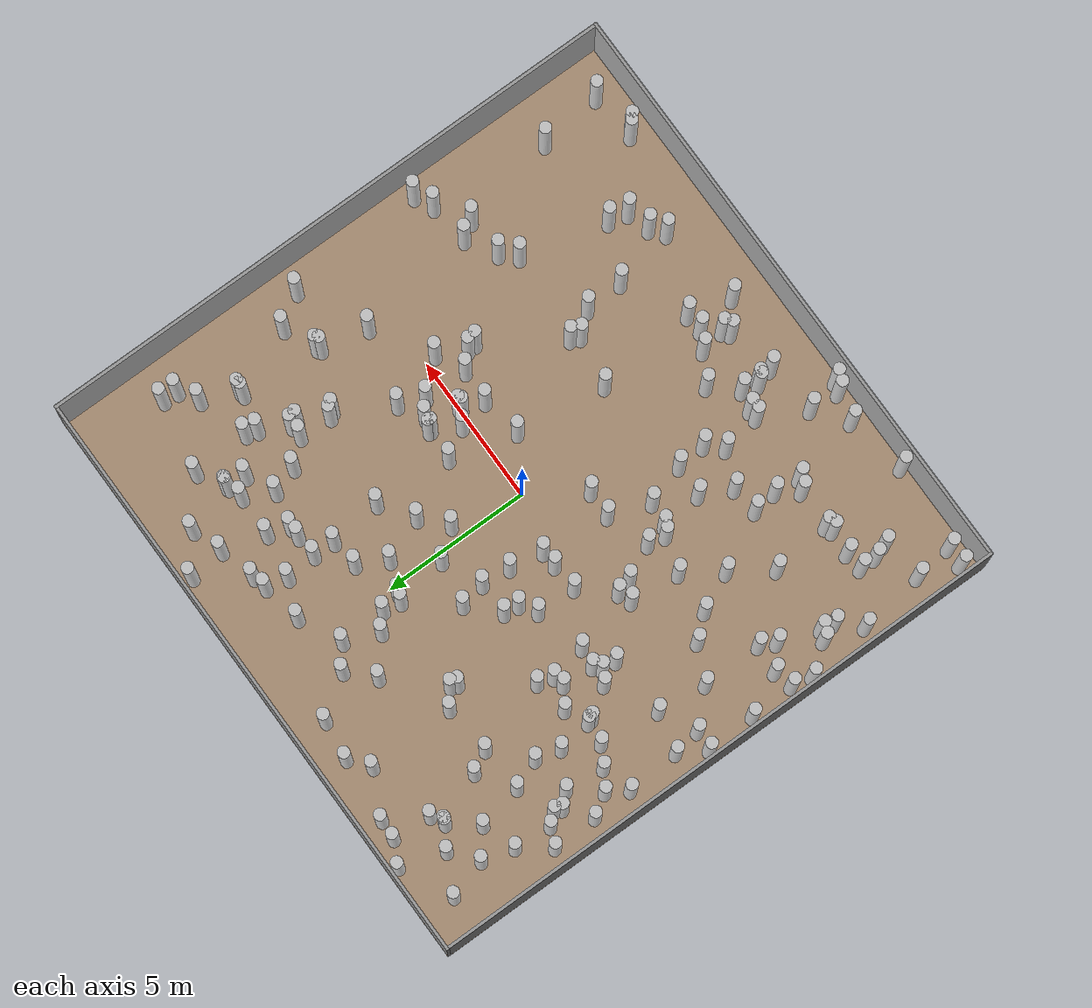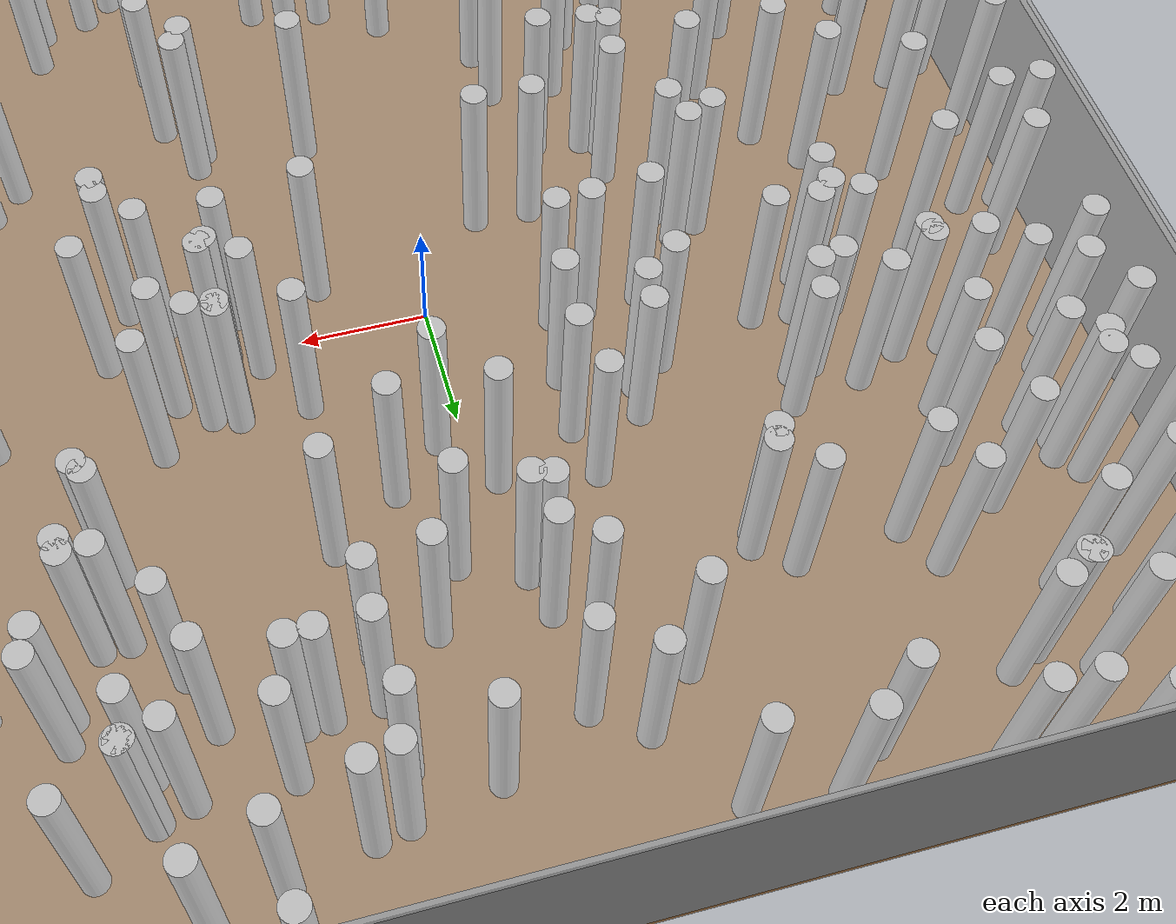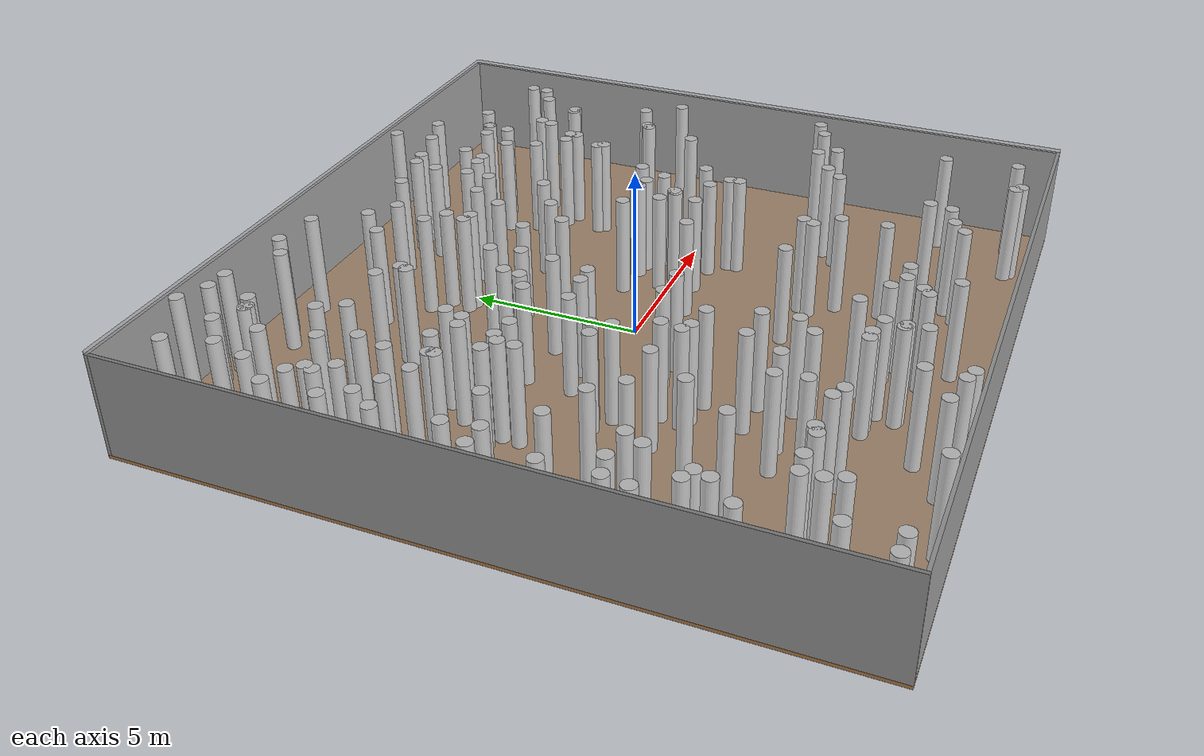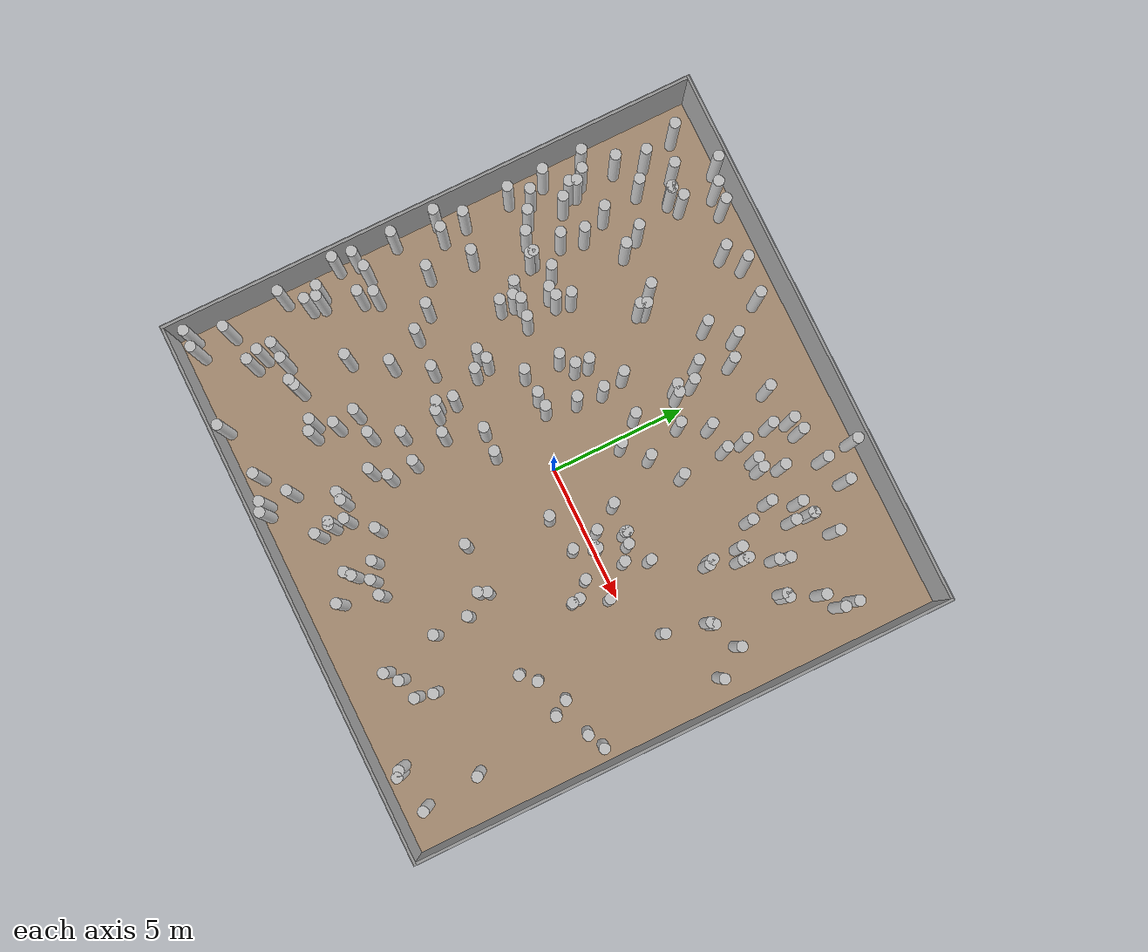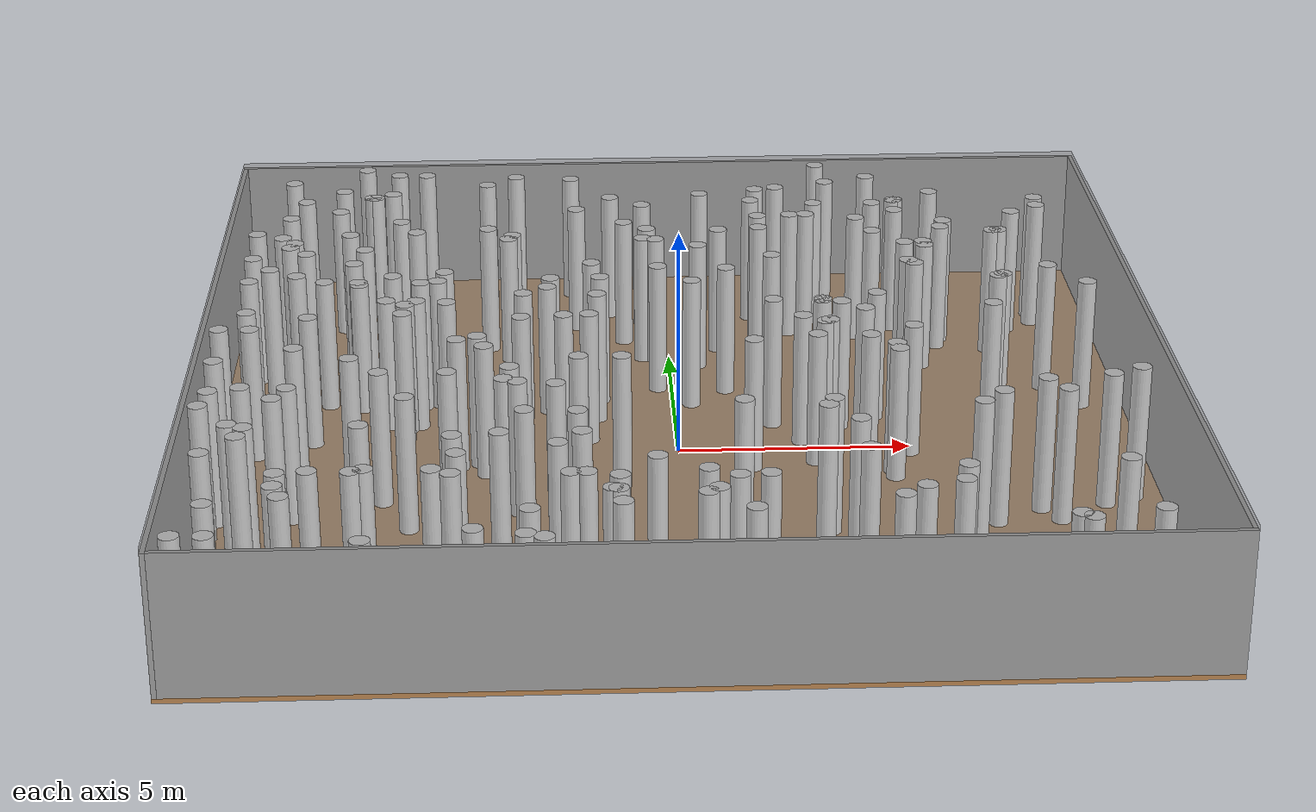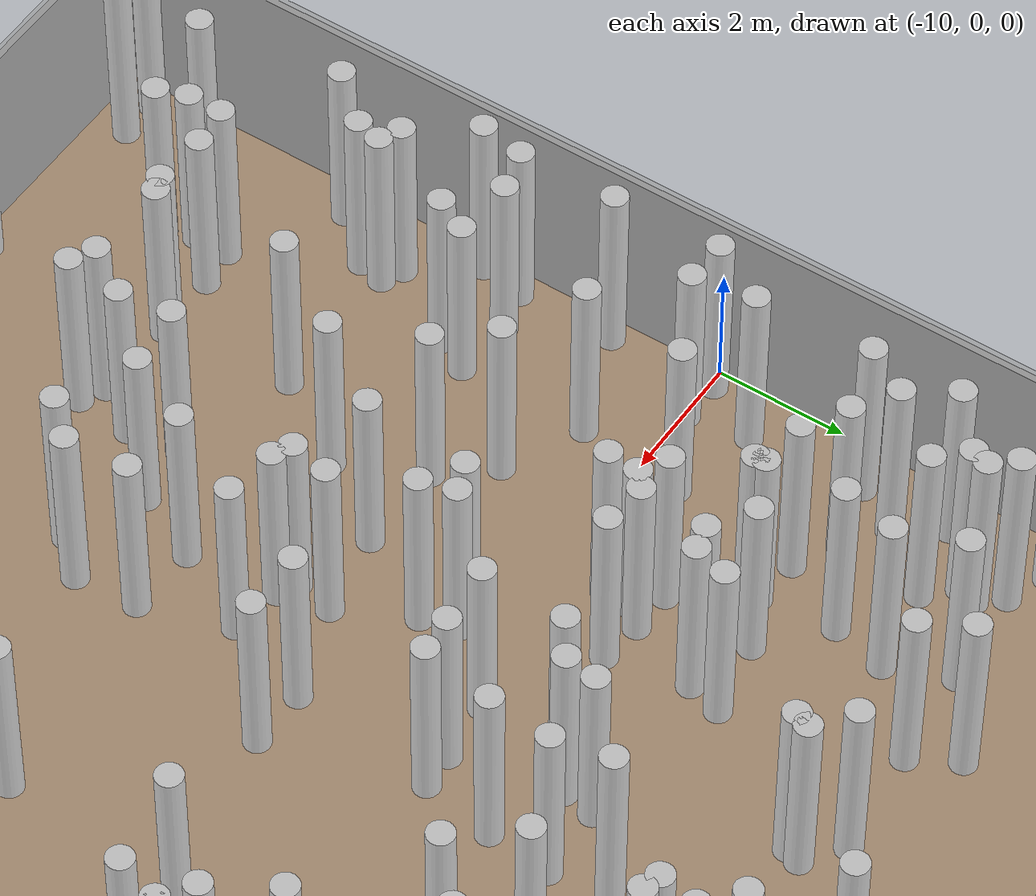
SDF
<?xml version="1.0" ?>
<sdf version="1.5">
  <world name="default">

    <include>
      <uri>model://sun</uri>
    </include>

    <physics name="default_physics" default="0" type="ode">
      <gravity>0 0 -9.8066</gravity>
      <ode>
        <solver>
          <type>quick</type>
          <iters>10</iters>
          <sor>1.3</sor>
          <use_dynamic_moi_rescaling>0</use_dynamic_moi_rescaling>
        </solver>
        <constraints>
          <cfm>0</cfm>
          <erp>0.2</erp>
          <contact_max_correcting_vel>100</contact_max_correcting_vel>
          <contact_surface_layer>0.001</contact_surface_layer>
        </constraints>
      </ode>
      <max_step_size>0.004</max_step_size>
      <real_time_factor>1</real_time_factor>
      <real_time_update_rate>250</real_time_update_rate>
      <magnetic_field>6.0e-6 2.3e-5 -4.2e-5</magnetic_field>
    </physics>

    <model name="box_1">
      <pose>0.04999999999999982 -10.05 1.5  0 0 0</pose>
      <static>true</static>
      <link name="link">
        <collision name="collision">
          <geometry>
            <box>
              <size>20.1 0.09999999999999964 3.0 </size>
            </box>
          </geometry>
        </collision>
        <visual name="visual">
          <geometry>
            <box>
              <size>20.1 0.09999999999999964 3.0 </size>
            </box>
          </geometry>
          <material>
            <script>
              <name>Gazebo/Grey</name>
              <uri>file://media/materials/scripts/gazebo.material</uri>
            </script>
          </material>
        </visual>
      </link>
    </model>

    <model name="box_2">
      <pose>10.05 0.04999999999999982 1.5  0 0 0</pose>
      <static>true</static>
      <link name="link">
        <collision name="collision">
          <geometry>
            <box>
              <size>0.09999999999999964 20.1 3.0 </size>
            </box>
          </geometry>
        </collision>
        <visual name="visual">
          <geometry>
            <box>
              <size>0.09999999999999964 20.1 3.0 </size>
            </box>
          </geometry>
          <material>
            <script>
              <name>Gazebo/Grey</name>
              <uri>file://media/materials/scripts/gazebo.material</uri>
            </script>
          </material>
        </visual>
      </link>
    </model>

    <model name="box_3">
      <pose>-0.04999999999999982 10.05 1.5  0 0 0</pose>
      <static>true</static>
      <link name="link">
        <collision name="collision">
          <geometry>
            <box>
              <size>20.1 0.09999999999999964 3.0 </size>
            </box>
          </geometry>
        </collision>
        <visual name="visual">
          <geometry>
            <box>
              <size>20.1 0.09999999999999964 3.0 </size>
            </box>
          </geometry>
          <material>
            <script>
              <name>Gazebo/Grey</name>
              <uri>file://media/materials/scripts/gazebo.material</uri>
            </script>
          </material>
        </visual>
      </link>
    </model>

    <model name="box_4">
      <pose>-10.05 -0.04999999999999982 1.5  0 0 0</pose>
      <static>true</static>
      <link name="link">
        <collision name="collision">
          <geometry>
            <box>
              <size>0.09999999999999964 20.1 3.0 </size>
            </box>
          </geometry>
        </collision>
        <visual name="visual">
          <geometry>
            <box>
              <size>0.09999999999999964 20.1 3.0 </size>
            </box>
          </geometry>
          <material>
            <script>
              <name>Gazebo/Grey</name>
              <uri>file://media/materials/scripts/gazebo.material</uri>
            </script>
          </material>
        </visual>
      </link>
    </model>

    <model name="box_5">
      <pose>0.0 0.0 -0.05  0 0 0</pose>
      <static>true</static>
      <link name="link">
        <collision name="collision">
          <geometry>
            <box>
              <size>20.2 20.2 0.1 </size>
            </box>
          </geometry>
        </collision>
        <visual name="visual">
          <geometry>
            <box>
              <size>20.2 20.2 0.1 </size>
            </box>
          </geometry>
          <material>
            <script>
              <name>Gazebo/WoodFloor</name>
              <uri>file://media/materials/scripts/gazebo.material</uri>
            </script>
          </material>
        </visual>
      </link>
    </model>

    <model name="box_6">
      <pose>0.0 0.0 3.05  0 0 0</pose>
      <static>true</static>
      <link name="link">
        <collision name="collision">
          <geometry>
            <box>
              <size>20.2 20.2 0.10000000000000009 </size>
            </box>
          </geometry>
        </collision>
        <visual name="visual">
          <geometry>
            <box>
              <size>20.2 20.2 0.10000000000000009 </size>
            </box>
          </geometry>
          <material>
            <script>
              <name>Gazebo/GreyTransparent</name>
              <uri>file://media/materials/scripts/gazebo.material</uri>
            </script>
          </material>
        </visual>
      </link>
    </model>

    <model name="cylinder_1">
      <pose>-4.66243172333 -5.36758389289 1.5  0 0 0</pose>
      <static>true</static>
      <link name="link">
        <collision name="collision">
          <geometry>
            <cylinder>
              <radius>0.2 </radius>
              <length>3.0 </length>
            </cylinder>
          </geometry>
        </collision>
        <visual name="visual">
          <geometry>
            <cylinder>
              <radius>0.2 </radius>
              <length>3.0 </length>
            </cylinder>
          </geometry>
          <material>
            <script>
              <name>Gazebo/White</name>
              <uri>file://media/materials/scripts/gazebo.material</uri>
            </script>
          </material>
        </visual>
      </link>
    </model>

    <model name="cylinder_2">
      <pose>-8.91809387741 3.40740717067 1.5  0 0 0</pose>
      <static>true</static>
      <link name="link">
        <collision name="collision">
          <geometry>
            <cylinder>
              <radius>0.2 </radius>
              <length>3.0 </length>
            </cylinder>
          </geometry>
        </collision>
        <visual name="visual">
          <geometry>
            <cylinder>
              <radius>0.2 </radius>
              <length>3.0 </length>
            </cylinder>
          </geometry>
          <material>
            <script>
              <name>Gazebo/White</name>
              <uri>file://media/materials/scripts/gazebo.material</uri>
            </script>
          </material>
        </visual>
      </link>
    </model>

    <model name="cylinder_3">
      <pose>-3.57165334212 5.28644316603 1.5  0 0 0</pose>
      <static>true</static>
      <link name="link">
        <collision name="collision">
          <geometry>
            <cylinder>
              <radius>0.2 </radius>
              <length>3.0 </length>
            </cylinder>
          </geometry>
        </collision>
        <visual name="visual">
          <geometry>
            <cylinder>
              <radius>0.2 </radius>
              <length>3.0 </length>
            </cylinder>
          </geometry>
          <material>
            <script>
              <name>Gazebo/White</name>
              <uri>file://media/materials/scripts/gazebo.material</uri>
            </script>
          </material>
        </visual>
      </link>
    </model>

    <model name="cylinder_4">
      <pose>-8.85773805694 -5.24153846135 1.5  0 0 0</pose>
      <static>true</static>
      <link name="link">
        <collision name="collision">
          <geometry>
            <cylinder>
              <radius>0.2 </radius>
              <length>3.0 </length>
            </cylinder>
          </geometry>
        </collision>
        <visual name="visual">
          <geometry>
            <cylinder>
              <radius>0.2 </radius>
              <length>3.0 </length>
            </cylinder>
          </geometry>
          <material>
            <script>
              <name>Gazebo/White</name>
              <uri>file://media/materials/scripts/gazebo.material</uri>
            </script>
          </material>
        </visual>
      </link>
    </model>

    <model name="cylinder_5">
      <pose>-6.40461813006 8.08408559015 1.5  0 0 0</pose>
      <static>true</static>
      <link name="link">
        <collision name="collision">
          <geometry>
            <cylinder>
              <radius>0.2 </radius>
              <length>3.0 </length>
            </cylinder>
          </geometry>
        </collision>
        <visual name="visual">
          <geometry>
            <cylinder>
              <radius>0.2 </radius>
              <length>3.0 </length>
            </cylinder>
          </geometry>
          <material>
            <script>
              <name>Gazebo/White</name>
              <uri>file://media/materials/scripts/gazebo.material</uri>
            </script>
          </material>
        </visual>
      </link>
    </model>

    <model name="cylinder_6">
      <pose>4.32921830737 -7.92791273874 1.5  0 0 0</pose>
      <static>true</static>
      <link name="link">
        <collision name="collision">
          <geometry>
            <cylinder>
              <radius>0.2 </radius>
              <length>3.0 </length>
            </cylinder>
          </geometry>
        </collision>
        <visual name="visual">
          <geometry>
            <cylinder>
              <radius>0.2 </radius>
              <length>3.0 </length>
            </cylinder>
          </geometry>
          <material>
            <script>
              <name>Gazebo/White</name>
              <uri>file://media/materials/scripts/gazebo.material</uri>
            </script>
          </material>
        </visual>
      </link>
    </model>

    <model name="cylinder_7">
      <pose>-9.35590509319 4.09018197456 1.5  0 0 0</pose>
      <static>true</static>
      <link name="link">
        <collision name="collision">
          <geometry>
            <cylinder>
              <radius>0.2 </radius>
              <length>3.0 </length>
            </cylinder>
          </geometry>
        </collision>
        <visual name="visual">
          <geometry>
            <cylinder>
              <radius>0.2 </radius>
              <length>3.0 </length>
            </cylinder>
          </geometry>
          <material>
            <script>
              <name>Gazebo/White</name>
              <uri>file://media/materials/scripts/gazebo.material</uri>
            </script>
          </material>
        </visual>
      </link>
    </model>

    <model name="cylinder_8">
      <pose>-3.40188709646 -2.85493463166 1.5  0 0 0</pose>
      <static>true</static>
      <link name="link">
        <collision name="collision">
          <geometry>
            <cylinder>
              <radius>0.2 </radius>
              <length>3.0 </length>
            </cylinder>
          </geometry>
        </collision>
        <visual name="visual">
          <geometry>
            <cylinder>
              <radius>0.2 </radius>
              <length>3.0 </length>
            </cylinder>
          </geometry>
          <material>
            <script>
              <name>Gazebo/White</name>
              <uri>file://media/materials/scripts/gazebo.material</uri>
            </script>
          </material>
        </visual>
      </link>
    </model>

    <model name="cylinder_9">
      <pose>7.42917851312 5.15135414426 1.5  0 0 0</pose>
      <static>true</static>
      <link name="link">
        <collision name="collision">
          <geometry>
            <cylinder>
              <radius>0.2 </radius>
              <length>3.0 </length>
            </cylinder>
          </geometry>
        </collision>
        <visual name="visual">
          <geometry>
            <cylinder>
              <radius>0.2 </radius>
              <length>3.0 </length>
            </cylinder>
          </geometry>
          <material>
            <script>
              <name>Gazebo/White</name>
              <uri>file://media/materials/scripts/gazebo.material</uri>
            </script>
          </material>
        </visual>
      </link>
    </model>

    <model name="cylinder_10">
      <pose>-6.18407992831 2.91278318849 1.5  0 0 0</pose>
      <static>true</static>
      <link name="link">
        <collision name="collision">
          <geometry>
            <cylinder>
              <radius>0.2 </radius>
              <length>3.0 </length>
            </cylinder>
          </geometry>
        </collision>
        <visual name="visual">
          <geometry>
            <cylinder>
              <radius>0.2 </radius>
              <length>3.0 </length>
            </cylinder>
          </geometry>
          <material>
            <script>
              <name>Gazebo/White</name>
              <uri>file://media/materials/scripts/gazebo.material</uri>
            </script>
          </material>
        </visual>
      </link>
    </model>

    <model name="cylinder_11">
      <pose>7.22114570087 -9.35978023825 1.5  0 0 0</pose>
      <static>true</static>
      <link name="link">
        <collision name="collision">
          <geometry>
            <cylinder>
              <radius>0.2 </radius>
              <length>3.0 </length>
            </cylinder>
          </geometry>
        </collision>
        <visual name="visual">
          <geometry>
            <cylinder>
              <radius>0.2 </radius>
              <length>3.0 </length>
            </cylinder>
          </geometry>
          <material>
            <script>
              <name>Gazebo/White</name>
              <uri>file://media/materials/scripts/gazebo.material</uri>
            </script>
          </material>
        </visual>
      </link>
    </model>

    <model name="cylinder_12">
      <pose>-7.07911922613 3.68708130066 1.5  0 0 0</pose>
      <static>true</static>
      <link name="link">
        <collision name="collision">
          <geometry>
            <cylinder>
              <radius>0.2 </radius>
              <length>3.0 </length>
            </cylinder>
          </geometry>
        </collision>
        <visual name="visual">
          <geometry>
            <cylinder>
              <radius>0.2 </radius>
              <length>3.0 </length>
            </cylinder>
          </geometry>
          <material>
            <script>
              <name>Gazebo/White</name>
              <uri>file://media/materials/scripts/gazebo.material</uri>
            </script>
          </material>
        </visual>
      </link>
    </model>

    <model name="cylinder_13">
      <pose>-0.603429975117 4.98804520344 1.5  0 0 0</pose>
      <static>true</static>
      <link name="link">
        <collision name="collision">
          <geometry>
            <cylinder>
              <radius>0.2 </radius>
              <length>3.0 </length>
            </cylinder>
          </geometry>
        </collision>
        <visual name="visual">
          <geometry>
            <cylinder>
              <radius>0.2 </radius>
              <length>3.0 </length>
            </cylinder>
          </geometry>
          <material>
            <script>
              <name>Gazebo/White</name>
              <uri>file://media/materials/scripts/gazebo.material</uri>
            </script>
          </material>
        </visual>
      </link>
    </model>

    <model name="cylinder_14">
      <pose>-4.56201192334 -6.16913718312 1.5  0 0 0</pose>
      <static>true</static>
      <link name="link">
        <collision name="collision">
          <geometry>
            <cylinder>
              <radius>0.2 </radius>
              <length>3.0 </length>
            </cylinder>
          </geometry>
        </collision>
        <visual name="visual">
          <geometry>
            <cylinder>
              <radius>0.2 </radius>
              <length>3.0 </length>
            </cylinder>
          </geometry>
          <material>
            <script>
              <name>Gazebo/White</name>
              <uri>file://media/materials/scripts/gazebo.material</uri>
            </script>
          </material>
        </visual>
      </link>
    </model>

    <model name="cylinder_15">
      <pose>0.389787638363 2.38360374222 1.5  0 0 0</pose>
      <static>true</static>
      <link name="link">
        <collision name="collision">
          <geometry>
            <cylinder>
              <radius>0.2 </radius>
              <length>3.0 </length>
            </cylinder>
          </geometry>
        </collision>
        <visual name="visual">
          <geometry>
            <cylinder>
              <radius>0.2 </radius>
              <length>3.0 </length>
            </cylinder>
          </geometry>
          <material>
            <script>
              <name>Gazebo/White</name>
              <uri>file://media/materials/scripts/gazebo.material</uri>
            </script>
          </material>
        </visual>
      </link>
    </model>

    <model name="cylinder_16">
      <pose>-8.48771588368 4.98800820012 1.5  0 0 0</pose>
      <static>true</static>
      <link name="link">
        <collision name="collision">
          <geometry>
            <cylinder>
              <radius>0.2 </radius>
              <length>3.0 </length>
            </cylinder>
          </geometry>
        </collision>
        <visual name="visual">
          <geometry>
            <cylinder>
              <radius>0.2 </radius>
              <length>3.0 </length>
            </cylinder>
          </geometry>
          <material>
            <script>
              <name>Gazebo/White</name>
              <uri>file://media/materials/scripts/gazebo.material</uri>
            </script>
          </material>
        </visual>
      </link>
    </model>

    <model name="cylinder_17">
      <pose>-9.06560502916 0.0428111366953 1.5  0 0 0</pose>
      <static>true</static>
      <link name="link">
        <collision name="collision">
          <geometry>
            <cylinder>
              <radius>0.2 </radius>
              <length>3.0 </length>
            </cylinder>
          </geometry>
        </collision>
        <visual name="visual">
          <geometry>
            <cylinder>
              <radius>0.2 </radius>
              <length>3.0 </length>
            </cylinder>
          </geometry>
          <material>
            <script>
              <name>Gazebo/White</name>
              <uri>file://media/materials/scripts/gazebo.material</uri>
            </script>
          </material>
        </visual>
      </link>
    </model>

    <model name="cylinder_18">
      <pose>5.75627242643 4.52410663655 1.5  0 0 0</pose>
      <static>true</static>
      <link name="link">
        <collision name="collision">
          <geometry>
            <cylinder>
              <radius>0.2 </radius>
              <length>3.0 </length>
            </cylinder>
          </geometry>
        </collision>
        <visual name="visual">
          <geometry>
            <cylinder>
              <radius>0.2 </radius>
              <length>3.0 </length>
            </cylinder>
          </geometry>
          <material>
            <script>
              <name>Gazebo/White</name>
              <uri>file://media/materials/scripts/gazebo.material</uri>
            </script>
          </material>
        </visual>
      </link>
    </model>

    <model name="cylinder_19">
      <pose>3.14257789734 -0.00227278770985 1.5  0 0 0</pose>
      <static>true</static>
      <link name="link">
        <collision name="collision">
          <geometry>
            <cylinder>
              <radius>0.2 </radius>
              <length>3.0 </length>
            </cylinder>
          </geometry>
        </collision>
        <visual name="visual">
          <geometry>
            <cylinder>
              <radius>0.2 </radius>
              <length>3.0 </length>
            </cylinder>
          </geometry>
          <material>
            <script>
              <name>Gazebo/White</name>
              <uri>file://media/materials/scripts/gazebo.material</uri>
            </script>
          </material>
        </visual>
      </link>
    </model>

    <model name="cylinder_20">
      <pose>8.61983563259 -9.05113959031 1.5  0 0 0</pose>
      <static>true</static>
      <link name="link">
        <collision name="collision">
          <geometry>
            <cylinder>
              <radius>0.2 </radius>
              <length>3.0 </length>
            </cylinder>
          </geometry>
        </collision>
        <visual name="visual">
          <geometry>
            <cylinder>
              <radius>0.2 </radius>
              <length>3.0 </length>
            </cylinder>
          </geometry>
          <material>
            <script>
              <name>Gazebo/White</name>
              <uri>file://media/materials/scripts/gazebo.material</uri>
            </script>
          </material>
        </visual>
      </link>
    </model>

    <model name="cylinder_21">
      <pose>-9.08391895157 -4.67856192585 1.5  0 0 0</pose>
      <static>true</static>
      <link name="link">
        <collision name="collision">
          <geometry>
            <cylinder>
              <radius>0.2 </radius>
              <length>3.0 </length>
            </cylinder>
          </geometry>
        </collision>
        <visual name="visual">
          <geometry>
            <cylinder>
              <radius>0.2 </radius>
              <length>3.0 </length>
            </cylinder>
          </geometry>
          <material>
            <script>
              <name>Gazebo/White</name>
              <uri>file://media/materials/scripts/gazebo.material</uri>
            </script>
          </material>
        </visual>
      </link>
    </model>

    <model name="cylinder_22">
      <pose>7.72255220808 -3.67734111971 1.5  0 0 0</pose>
      <static>true</static>
      <link name="link">
        <collision name="collision">
          <geometry>
            <cylinder>
              <radius>0.2 </radius>
              <length>3.0 </length>
            </cylinder>
          </geometry>
        </collision>
        <visual name="visual">
          <geometry>
            <cylinder>
              <radius>0.2 </radius>
              <length>3.0 </length>
            </cylinder>
          </geometry>
          <material>
            <script>
              <name>Gazebo/White</name>
              <uri>file://media/materials/scripts/gazebo.material</uri>
            </script>
          </material>
        </visual>
      </link>
    </model>

    <model name="cylinder_23">
      <pose>-8.05006033049 -2.99132176691 1.5  0 0 0</pose>
      <static>true</static>
      <link name="link">
        <collision name="collision">
          <geometry>
            <cylinder>
              <radius>0.2 </radius>
              <length>3.0 </length>
            </cylinder>
          </geometry>
        </collision>
        <visual name="visual">
          <geometry>
            <cylinder>
              <radius>0.2 </radius>
              <length>3.0 </length>
            </cylinder>
          </geometry>
          <material>
            <script>
              <name>Gazebo/White</name>
              <uri>file://media/materials/scripts/gazebo.material</uri>
            </script>
          </material>
        </visual>
      </link>
    </model>

    <model name="cylinder_24">
      <pose>-2.11901545174 -5.2703255166 1.5  0 0 0</pose>
      <static>true</static>
      <link name="link">
        <collision name="collision">
          <geometry>
            <cylinder>
              <radius>0.2 </radius>
              <length>3.0 </length>
            </cylinder>
          </geometry>
        </collision>
        <visual name="visual">
          <geometry>
            <cylinder>
              <radius>0.2 </radius>
              <length>3.0 </length>
            </cylinder>
          </geometry>
          <material>
            <script>
              <name>Gazebo/White</name>
              <uri>file://media/materials/scripts/gazebo.material</uri>
            </script>
          </material>
        </visual>
      </link>
    </model>

    <model name="cylinder_25">
      <pose>3.8813494245 -8.28580532006 1.5  0 0 0</pose>
      <static>true</static>
      <link name="link">
        <collision name="collision">
          <geometry>
            <cylinder>
              <radius>0.2 </radius>
              <length>3.0 </length>
            </cylinder>
          </geometry>
        </collision>
        <visual name="visual">
          <geometry>
            <cylinder>
              <radius>0.2 </radius>
              <length>3.0 </length>
            </cylinder>
          </geometry>
          <material>
            <script>
              <name>Gazebo/White</name>
              <uri>file://media/materials/scripts/gazebo.material</uri>
            </script>
          </material>
        </visual>
      </link>
    </model>

    <model name="cylinder_26">
      <pose>8.68435972278 6.73024260488 1.5  0 0 0</pose>
      <static>true</static>
      <link name="link">
        <collision name="collision">
          <geometry>
            <cylinder>
              <radius>0.2 </radius>
              <length>3.0 </length>
            </cylinder>
          </geometry>
        </collision>
        <visual name="visual">
          <geometry>
            <cylinder>
              <radius>0.2 </radius>
              <length>3.0 </length>
            </cylinder>
          </geometry>
          <material>
            <script>
              <name>Gazebo/White</name>
              <uri>file://media/materials/scripts/gazebo.material</uri>
            </script>
          </material>
        </visual>
      </link>
    </model>

    <model name="cylinder_27">
      <pose>1.19057691846 3.10215745725 1.5  0 0 0</pose>
      <static>true</static>
      <link name="link">
        <collision name="collision">
          <geometry>
            <cylinder>
              <radius>0.2 </radius>
              <length>3.0 </length>
            </cylinder>
          </geometry>
        </collision>
        <visual name="visual">
          <geometry>
            <cylinder>
              <radius>0.2 </radius>
              <length>3.0 </length>
            </cylinder>
          </geometry>
          <material>
            <script>
              <name>Gazebo/White</name>
              <uri>file://media/materials/scripts/gazebo.material</uri>
            </script>
          </material>
        </visual>
      </link>
    </model>

    <model name="cylinder_28">
      <pose>8.71213821655 7.2407370728 1.5  0 0 0</pose>
      <static>true</static>
      <link name="link">
        <collision name="collision">
          <geometry>
            <cylinder>
              <radius>0.2 </radius>
              <length>3.0 </length>
            </cylinder>
          </geometry>
        </collision>
        <visual name="visual">
          <geometry>
            <cylinder>
              <radius>0.2 </radius>
              <length>3.0 </length>
            </cylinder>
          </geometry>
          <material>
            <script>
              <name>Gazebo/White</name>
              <uri>file://media/materials/scripts/gazebo.material</uri>
            </script>
          </material>
        </visual>
      </link>
    </model>

    <model name="cylinder_29">
      <pose>0.215602446316 -8.02795895449 1.5  0 0 0</pose>
      <static>true</static>
      <link name="link">
        <collision name="collision">
          <geometry>
            <cylinder>
              <radius>0.2 </radius>
              <length>3.0 </length>
            </cylinder>
          </geometry>
        </collision>
        <visual name="visual">
          <geometry>
            <cylinder>
              <radius>0.2 </radius>
              <length>3.0 </length>
            </cylinder>
          </geometry>
          <material>
            <script>
              <name>Gazebo/White</name>
              <uri>file://media/materials/scripts/gazebo.material</uri>
            </script>
          </material>
        </visual>
      </link>
    </model>

    <model name="cylinder_30">
      <pose>-8.98854296439 -2.91839689633 1.5  0 0 0</pose>
      <static>true</static>
      <link name="link">
        <collision name="collision">
          <geometry>
            <cylinder>
              <radius>0.2 </radius>
              <length>3.0 </length>
            </cylinder>
          </geometry>
        </collision>
        <visual name="visual">
          <geometry>
            <cylinder>
              <radius>0.2 </radius>
              <length>3.0 </length>
            </cylinder>
          </geometry>
          <material>
            <script>
              <name>Gazebo/White</name>
              <uri>file://media/materials/scripts/gazebo.material</uri>
            </script>
          </material>
        </visual>
      </link>
    </model>

    <model name="cylinder_31">
      <pose>5.41172631743 3.23236437206 1.5  0 0 0</pose>
      <static>true</static>
      <link name="link">
        <collision name="collision">
          <geometry>
            <cylinder>
              <radius>0.2 </radius>
              <length>3.0 </length>
            </cylinder>
          </geometry>
        </collision>
        <visual name="visual">
          <geometry>
            <cylinder>
              <radius>0.2 </radius>
              <length>3.0 </length>
            </cylinder>
          </geometry>
          <material>
            <script>
              <name>Gazebo/White</name>
              <uri>file://media/materials/scripts/gazebo.material</uri>
            </script>
          </material>
        </visual>
      </link>
    </model>

    <model name="cylinder_32">
      <pose>-3.20127014619 -9.59197432469 1.5  0 0 0</pose>
      <static>true</static>
      <link name="link">
        <collision name="collision">
          <geometry>
            <cylinder>
              <radius>0.2 </radius>
              <length>3.0 </length>
            </cylinder>
          </geometry>
        </collision>
        <visual name="visual">
          <geometry>
            <cylinder>
              <radius>0.2 </radius>
              <length>3.0 </length>
            </cylinder>
          </geometry>
          <material>
            <script>
              <name>Gazebo/White</name>
              <uri>file://media/materials/scripts/gazebo.material</uri>
            </script>
          </material>
        </visual>
      </link>
    </model>

    <model name="cylinder_33">
      <pose>6.84010754183 0.846771831331 1.5  0 0 0</pose>
      <static>true</static>
      <link name="link">
        <collision name="collision">
          <geometry>
            <cylinder>
              <radius>0.2 </radius>
              <length>3.0 </length>
            </cylinder>
          </geometry>
        </collision>
        <visual name="visual">
          <geometry>
            <cylinder>
              <radius>0.2 </radius>
              <length>3.0 </length>
            </cylinder>
          </geometry>
          <material>
            <script>
              <name>Gazebo/White</name>
              <uri>file://media/materials/scripts/gazebo.material</uri>
            </script>
          </material>
        </visual>
      </link>
    </model>

    <model name="cylinder_34">
      <pose>2.11115818259 1.23667951528 1.5  0 0 0</pose>
      <static>true</static>
      <link name="link">
        <collision name="collision">
          <geometry>
            <cylinder>
              <radius>0.2 </radius>
              <length>3.0 </length>
            </cylinder>
          </geometry>
        </collision>
        <visual name="visual">
          <geometry>
            <cylinder>
              <radius>0.2 </radius>
              <length>3.0 </length>
            </cylinder>
          </geometry>
          <material>
            <script>
              <name>Gazebo/White</name>
              <uri>file://media/materials/scripts/gazebo.material</uri>
            </script>
          </material>
        </visual>
      </link>
    </model>

    <model name="cylinder_35">
      <pose>5.33574317188 4.49939920938 1.5  0 0 0</pose>
      <static>true</static>
      <link name="link">
        <collision name="collision">
          <geometry>
            <cylinder>
              <radius>0.2 </radius>
              <length>3.0 </length>
            </cylinder>
          </geometry>
        </collision>
        <visual name="visual">
          <geometry>
            <cylinder>
              <radius>0.2 </radius>
              <length>3.0 </length>
            </cylinder>
          </geometry>
          <material>
            <script>
              <name>Gazebo/White</name>
              <uri>file://media/materials/scripts/gazebo.material</uri>
            </script>
          </material>
        </visual>
      </link>
    </model>

    <model name="cylinder_36">
      <pose>4.38933233178 1.52820655671 1.5  0 0 0</pose>
      <static>true</static>
      <link name="link">
        <collision name="collision">
          <geometry>
            <cylinder>
              <radius>0.2 </radius>
              <length>3.0 </length>
            </cylinder>
          </geometry>
        </collision>
        <visual name="visual">
          <geometry>
            <cylinder>
              <radius>0.2 </radius>
              <length>3.0 </length>
            </cylinder>
          </geometry>
          <material>
            <script>
              <name>Gazebo/White</name>
              <uri>file://media/materials/scripts/gazebo.material</uri>
            </script>
          </material>
        </visual>
      </link>
    </model>

    <model name="cylinder_37">
      <pose>-7.96819840306 -6.91413932885 1.5  0 0 0</pose>
      <static>true</static>
      <link name="link">
        <collision name="collision">
          <geometry>
            <cylinder>
              <radius>0.2 </radius>
              <length>3.0 </length>
            </cylinder>
          </geometry>
        </collision>
        <visual name="visual">
          <geometry>
            <cylinder>
              <radius>0.2 </radius>
              <length>3.0 </length>
            </cylinder>
          </geometry>
          <material>
            <script>
              <name>Gazebo/White</name>
              <uri>file://media/materials/scripts/gazebo.material</uri>
            </script>
          </material>
        </visual>
      </link>
    </model>

    <model name="cylinder_38">
      <pose>8.75683538604 -2.98014474971 1.5  0 0 0</pose>
      <static>true</static>
      <link name="link">
        <collision name="collision">
          <geometry>
            <cylinder>
              <radius>0.2 </radius>
              <length>3.0 </length>
            </cylinder>
          </geometry>
        </collision>
        <visual name="visual">
          <geometry>
            <cylinder>
              <radius>0.2 </radius>
              <length>3.0 </length>
            </cylinder>
          </geometry>
          <material>
            <script>
              <name>Gazebo/White</name>
              <uri>file://media/materials/scripts/gazebo.material</uri>
            </script>
          </material>
        </visual>
      </link>
    </model>

    <model name="cylinder_39">
      <pose>-2.7844474214 2.16016347226 1.5  0 0 0</pose>
      <static>true</static>
      <link name="link">
        <collision name="collision">
          <geometry>
            <cylinder>
              <radius>0.2 </radius>
              <length>3.0 </length>
            </cylinder>
          </geometry>
        </collision>
        <visual name="visual">
          <geometry>
            <cylinder>
              <radius>0.2 </radius>
              <length>3.0 </length>
            </cylinder>
          </geometry>
          <material>
            <script>
              <name>Gazebo/White</name>
              <uri>file://media/materials/scripts/gazebo.material</uri>
            </script>
          </material>
        </visual>
      </link>
    </model>

    <model name="cylinder_40">
      <pose>-2.44058042826 0.564239685322 1.5  0 0 0</pose>
      <static>true</static>
      <link name="link">
        <collision name="collision">
          <geometry>
            <cylinder>
              <radius>0.2 </radius>
              <length>3.0 </length>
            </cylinder>
          </geometry>
        </collision>
        <visual name="visual">
          <geometry>
            <cylinder>
              <radius>0.2 </radius>
              <length>3.0 </length>
            </cylinder>
          </geometry>
          <material>
            <script>
              <name>Gazebo/White</name>
              <uri>file://media/materials/scripts/gazebo.material</uri>
            </script>
          </material>
        </visual>
      </link>
    </model>

    <model name="cylinder_41">
      <pose>-1.42372645824 -7.24630831055 1.5  0 0 0</pose>
      <static>true</static>
      <link name="link">
        <collision name="collision">
          <geometry>
            <cylinder>
              <radius>0.2 </radius>
              <length>3.0 </length>
            </cylinder>
          </geometry>
        </collision>
        <visual name="visual">
          <geometry>
            <cylinder>
              <radius>0.2 </radius>
              <length>3.0 </length>
            </cylinder>
          </geometry>
          <material>
            <script>
              <name>Gazebo/White</name>
              <uri>file://media/materials/scripts/gazebo.material</uri>
            </script>
          </material>
        </visual>
      </link>
    </model>

    <model name="cylinder_42">
      <pose>7.17837514745 2.4030366884 1.5  0 0 0</pose>
      <static>true</static>
      <link name="link">
        <collision name="collision">
          <geometry>
            <cylinder>
              <radius>0.2 </radius>
              <length>3.0 </length>
            </cylinder>
          </geometry>
        </collision>
        <visual name="visual">
          <geometry>
            <cylinder>
              <radius>0.2 </radius>
              <length>3.0 </length>
            </cylinder>
          </geometry>
          <material>
            <script>
              <name>Gazebo/White</name>
              <uri>file://media/materials/scripts/gazebo.material</uri>
            </script>
          </material>
        </visual>
      </link>
    </model>

    <model name="cylinder_43">
      <pose>-6.79873943102 7.83938631427 1.5  0 0 0</pose>
      <static>true</static>
      <link name="link">
        <collision name="collision">
          <geometry>
            <cylinder>
              <radius>0.2 </radius>
              <length>3.0 </length>
            </cylinder>
          </geometry>
        </collision>
        <visual name="visual">
          <geometry>
            <cylinder>
              <radius>0.2 </radius>
              <length>3.0 </length>
            </cylinder>
          </geometry>
          <material>
            <script>
              <name>Gazebo/White</name>
              <uri>file://media/materials/scripts/gazebo.material</uri>
            </script>
          </material>
        </visual>
      </link>
    </model>

    <model name="cylinder_44">
      <pose>-8.29941449807 3.00940650877 1.5  0 0 0</pose>
      <static>true</static>
      <link name="link">
        <collision name="collision">
          <geometry>
            <cylinder>
              <radius>0.2 </radius>
              <length>3.0 </length>
            </cylinder>
          </geometry>
        </collision>
        <visual name="visual">
          <geometry>
            <cylinder>
              <radius>0.2 </radius>
              <length>3.0 </length>
            </cylinder>
          </geometry>
          <material>
            <script>
              <name>Gazebo/White</name>
              <uri>file://media/materials/scripts/gazebo.material</uri>
            </script>
          </material>
        </visual>
      </link>
    </model>

    <model name="cylinder_45">
      <pose>-9.32123799414 2.73283957312 1.5  0 0 0</pose>
      <static>true</static>
      <link name="link">
        <collision name="collision">
          <geometry>
            <cylinder>
              <radius>0.2 </radius>
              <length>3.0 </length>
            </cylinder>
          </geometry>
        </collision>
        <visual name="visual">
          <geometry>
            <cylinder>
              <radius>0.2 </radius>
              <length>3.0 </length>
            </cylinder>
          </geometry>
          <material>
            <script>
              <name>Gazebo/White</name>
              <uri>file://media/materials/scripts/gazebo.material</uri>
            </script>
          </material>
        </visual>
      </link>
    </model>

    <model name="cylinder_46">
      <pose>9.07430429218 1.96268823712 1.5  0 0 0</pose>
      <static>true</static>
      <link name="link">
        <collision name="collision">
          <geometry>
            <cylinder>
              <radius>0.2 </radius>
              <length>3.0 </length>
            </cylinder>
          </geometry>
        </collision>
        <visual name="visual">
          <geometry>
            <cylinder>
              <radius>0.2 </radius>
              <length>3.0 </length>
            </cylinder>
          </geometry>
          <material>
            <script>
              <name>Gazebo/White</name>
              <uri>file://media/materials/scripts/gazebo.material</uri>
            </script>
          </material>
        </visual>
      </link>
    </model>

    <model name="cylinder_47">
      <pose>-9.66109366104 -1.57732321205 1.5  0 0 0</pose>
      <static>true</static>
      <link name="link">
        <collision name="collision">
          <geometry>
            <cylinder>
              <radius>0.2 </radius>
              <length>3.0 </length>
            </cylinder>
          </geometry>
        </collision>
        <visual name="visual">
          <geometry>
            <cylinder>
              <radius>0.2 </radius>
              <length>3.0 </length>
            </cylinder>
          </geometry>
          <material>
            <script>
              <name>Gazebo/White</name>
              <uri>file://media/materials/scripts/gazebo.material</uri>
            </script>
          </material>
        </visual>
      </link>
    </model>

    <model name="cylinder_48">
      <pose>-0.496940937456 5.57991217325 1.5  0 0 0</pose>
      <static>true</static>
      <link name="link">
        <collision name="collision">
          <geometry>
            <cylinder>
              <radius>0.2 </radius>
              <length>3.0 </length>
            </cylinder>
          </geometry>
        </collision>
        <visual name="visual">
          <geometry>
            <cylinder>
              <radius>0.2 </radius>
              <length>3.0 </length>
            </cylinder>
          </geometry>
          <material>
            <script>
              <name>Gazebo/White</name>
              <uri>file://media/materials/scripts/gazebo.material</uri>
            </script>
          </material>
        </visual>
      </link>
    </model>

    <model name="cylinder_49">
      <pose>-6.8581710338 7.85588094173 1.5  0 0 0</pose>
      <static>true</static>
      <link name="link">
        <collision name="collision">
          <geometry>
            <cylinder>
              <radius>0.2 </radius>
              <length>3.0 </length>
            </cylinder>
          </geometry>
        </collision>
        <visual name="visual">
          <geometry>
            <cylinder>
              <radius>0.2 </radius>
              <length>3.0 </length>
            </cylinder>
          </geometry>
          <material>
            <script>
              <name>Gazebo/White</name>
              <uri>file://media/materials/scripts/gazebo.material</uri>
            </script>
          </material>
        </visual>
      </link>
    </model>

    <model name="cylinder_50">
      <pose>-6.19443365025 -9.76611396982 1.5  0 0 0</pose>
      <static>true</static>
      <link name="link">
        <collision name="collision">
          <geometry>
            <cylinder>
              <radius>0.2 </radius>
              <length>3.0 </length>
            </cylinder>
          </geometry>
        </collision>
        <visual name="visual">
          <geometry>
            <cylinder>
              <radius>0.2 </radius>
              <length>3.0 </length>
            </cylinder>
          </geometry>
          <material>
            <script>
              <name>Gazebo/White</name>
              <uri>file://media/materials/scripts/gazebo.material</uri>
            </script>
          </material>
        </visual>
      </link>
    </model>

    <model name="cylinder_51">
      <pose>-1.2532635501 -1.66249641853 1.5  0 0 0</pose>
      <static>true</static>
      <link name="link">
        <collision name="collision">
          <geometry>
            <cylinder>
              <radius>0.2 </radius>
              <length>3.0 </length>
            </cylinder>
          </geometry>
        </collision>
        <visual name="visual">
          <geometry>
            <cylinder>
              <radius>0.2 </radius>
              <length>3.0 </length>
            </cylinder>
          </geometry>
          <material>
            <script>
              <name>Gazebo/White</name>
              <uri>file://media/materials/scripts/gazebo.material</uri>
            </script>
          </material>
        </visual>
      </link>
    </model>

    <model name="cylinder_52">
      <pose>-4.26414238094 -0.504776513904 1.5  0 0 0</pose>
      <static>true</static>
      <link name="link">
        <collision name="collision">
          <geometry>
            <cylinder>
              <radius>0.2 </radius>
              <length>3.0 </length>
            </cylinder>
          </geometry>
        </collision>
        <visual name="visual">
          <geometry>
            <cylinder>
              <radius>0.2 </radius>
              <length>3.0 </length>
            </cylinder>
          </geometry>
          <material>
            <script>
              <name>Gazebo/White</name>
              <uri>file://media/materials/scripts/gazebo.material</uri>
            </script>
          </material>
        </visual>
      </link>
    </model>

    <model name="cylinder_53">
      <pose>-2.35902708184 -7.08958310026 1.5  0 0 0</pose>
      <static>true</static>
      <link name="link">
        <collision name="collision">
          <geometry>
            <cylinder>
              <radius>0.2 </radius>
              <length>3.0 </length>
            </cylinder>
          </geometry>
        </collision>
        <visual name="visual">
          <geometry>
            <cylinder>
              <radius>0.2 </radius>
              <length>3.0 </length>
            </cylinder>
          </geometry>
          <material>
            <script>
              <name>Gazebo/White</name>
              <uri>file://media/materials/scripts/gazebo.material</uri>
            </script>
          </material>
        </visual>
      </link>
    </model>

    <model name="cylinder_54">
      <pose>3.47068155479 7.07573758665 1.5  0 0 0</pose>
      <static>true</static>
      <link name="link">
        <collision name="collision">
          <geometry>
            <cylinder>
              <radius>0.2 </radius>
              <length>3.0 </length>
            </cylinder>
          </geometry>
        </collision>
        <visual name="visual">
          <geometry>
            <cylinder>
              <radius>0.2 </radius>
              <length>3.0 </length>
            </cylinder>
          </geometry>
          <material>
            <script>
              <name>Gazebo/White</name>
              <uri>file://media/materials/scripts/gazebo.material</uri>
            </script>
          </material>
        </visual>
      </link>
    </model>

    <model name="cylinder_55">
      <pose>6.28266629386 7.7297583857 1.5  0 0 0</pose>
      <static>true</static>
      <link name="link">
        <collision name="collision">
          <geometry>
            <cylinder>
              <radius>0.2 </radius>
              <length>3.0 </length>
            </cylinder>
          </geometry>
        </collision>
        <visual name="visual">
          <geometry>
            <cylinder>
              <radius>0.2 </radius>
              <length>3.0 </length>
            </cylinder>
          </geometry>
          <material>
            <script>
              <name>Gazebo/White</name>
              <uri>file://media/materials/scripts/gazebo.material</uri>
            </script>
          </material>
        </visual>
      </link>
    </model>

    <model name="cylinder_56">
      <pose>-6.26087689021 1.49954999286 1.5  0 0 0</pose>
      <static>true</static>
      <link name="link">
        <collision name="collision">
          <geometry>
            <cylinder>
              <radius>0.2 </radius>
              <length>3.0 </length>
            </cylinder>
          </geometry>
        </collision>
        <visual name="visual">
          <geometry>
            <cylinder>
              <radius>0.2 </radius>
              <length>3.0 </length>
            </cylinder>
          </geometry>
          <material>
            <script>
              <name>Gazebo/White</name>
              <uri>file://media/materials/scripts/gazebo.material</uri>
            </script>
          </material>
        </visual>
      </link>
    </model>

    <model name="cylinder_57">
      <pose>-5.61491477612 1.46301873385 1.5  0 0 0</pose>
      <static>true</static>
      <link name="link">
        <collision name="collision">
          <geometry>
            <cylinder>
              <radius>0.2 </radius>
              <length>3.0 </length>
            </cylinder>
          </geometry>
        </collision>
        <visual name="visual">
          <geometry>
            <cylinder>
              <radius>0.2 </radius>
              <length>3.0 </length>
            </cylinder>
          </geometry>
          <material>
            <script>
              <name>Gazebo/White</name>
              <uri>file://media/materials/scripts/gazebo.material</uri>
            </script>
          </material>
        </visual>
      </link>
    </model>

    <model name="cylinder_58">
      <pose>-4.1233433859 5.71170081979 1.5  0 0 0</pose>
      <static>true</static>
      <link name="link">
        <collision name="collision">
          <geometry>
            <cylinder>
              <radius>0.2 </radius>
              <length>3.0 </length>
            </cylinder>
          </geometry>
        </collision>
        <visual name="visual">
          <geometry>
            <cylinder>
              <radius>0.2 </radius>
              <length>3.0 </length>
            </cylinder>
          </geometry>
          <material>
            <script>
              <name>Gazebo/White</name>
              <uri>file://media/materials/scripts/gazebo.material</uri>
            </script>
          </material>
        </visual>
      </link>
    </model>

    <model name="cylinder_59">
      <pose>4.36966898715 6.09762204568 1.5  0 0 0</pose>
      <static>true</static>
      <link name="link">
        <collision name="collision">
          <geometry>
            <cylinder>
              <radius>0.2 </radius>
              <length>3.0 </length>
            </cylinder>
          </geometry>
        </collision>
        <visual name="visual">
          <geometry>
            <cylinder>
              <radius>0.2 </radius>
              <length>3.0 </length>
            </cylinder>
          </geometry>
          <material>
            <script>
              <name>Gazebo/White</name>
              <uri>file://media/materials/scripts/gazebo.material</uri>
            </script>
          </material>
        </visual>
      </link>
    </model>

    <model name="cylinder_60">
      <pose>5.93662151583 -4.20188149617 1.5  0 0 0</pose>
      <static>true</static>
      <link name="link">
        <collision name="collision">
          <geometry>
            <cylinder>
              <radius>0.2 </radius>
              <length>3.0 </length>
            </cylinder>
          </geometry>
        </collision>
        <visual name="visual">
          <geometry>
            <cylinder>
              <radius>0.2 </radius>
              <length>3.0 </length>
            </cylinder>
          </geometry>
          <material>
            <script>
              <name>Gazebo/White</name>
              <uri>file://media/materials/scripts/gazebo.material</uri>
            </script>
          </material>
        </visual>
      </link>
    </model>

    <model name="cylinder_61">
      <pose>-1.39293129773 -8.35965542722 1.5  0 0 0</pose>
      <static>true</static>
      <link name="link">
        <collision name="collision">
          <geometry>
            <cylinder>
              <radius>0.2 </radius>
              <length>3.0 </length>
            </cylinder>
          </geometry>
        </collision>
        <visual name="visual">
          <geometry>
            <cylinder>
              <radius>0.2 </radius>
              <length>3.0 </length>
            </cylinder>
          </geometry>
          <material>
            <script>
              <name>Gazebo/White</name>
              <uri>file://media/materials/scripts/gazebo.material</uri>
            </script>
          </material>
        </visual>
      </link>
    </model>

    <model name="cylinder_62">
      <pose>1.14145559018 5.46133663972 1.5  0 0 0</pose>
      <static>true</static>
      <link name="link">
        <collision name="collision">
          <geometry>
            <cylinder>
              <radius>0.2 </radius>
              <length>3.0 </length>
            </cylinder>
          </geometry>
        </collision>
        <visual name="visual">
          <geometry>
            <cylinder>
              <radius>0.2 </radius>
              <length>3.0 </length>
            </cylinder>
          </geometry>
          <material>
            <script>
              <name>Gazebo/White</name>
              <uri>file://media/materials/scripts/gazebo.material</uri>
            </script>
          </material>
        </visual>
      </link>
    </model>

    <model name="cylinder_63">
      <pose>-6.87695886852 4.52264266228 1.5  0 0 0</pose>
      <static>true</static>
      <link name="link">
        <collision name="collision">
          <geometry>
            <cylinder>
              <radius>0.2 </radius>
              <length>3.0 </length>
            </cylinder>
          </geometry>
        </collision>
        <visual name="visual">
          <geometry>
            <cylinder>
              <radius>0.2 </radius>
              <length>3.0 </length>
            </cylinder>
          </geometry>
          <material>
            <script>
              <name>Gazebo/White</name>
              <uri>file://media/materials/scripts/gazebo.material</uri>
            </script>
          </material>
        </visual>
      </link>
    </model>

    <model name="cylinder_64">
      <pose>-7.25736357598 5.46162269004 1.5  0 0 0</pose>
      <static>true</static>
      <link name="link">
        <collision name="collision">
          <geometry>
            <cylinder>
              <radius>0.2 </radius>
              <length>3.0 </length>
            </cylinder>
          </geometry>
        </collision>
        <visual name="visual">
          <geometry>
            <cylinder>
              <radius>0.2 </radius>
              <length>3.0 </length>
            </cylinder>
          </geometry>
          <material>
            <script>
              <name>Gazebo/White</name>
              <uri>file://media/materials/scripts/gazebo.material</uri>
            </script>
          </material>
        </visual>
      </link>
    </model>

    <model name="cylinder_65">
      <pose>8.36405707521 -6.9270664571 1.5  0 0 0</pose>
      <static>true</static>
      <link name="link">
        <collision name="collision">
          <geometry>
            <cylinder>
              <radius>0.2 </radius>
              <length>3.0 </length>
            </cylinder>
          </geometry>
        </collision>
        <visual name="visual">
          <geometry>
            <cylinder>
              <radius>0.2 </radius>
              <length>3.0 </length>
            </cylinder>
          </geometry>
          <material>
            <script>
              <name>Gazebo/White</name>
              <uri>file://media/materials/scripts/gazebo.material</uri>
            </script>
          </material>
        </visual>
      </link>
    </model>

    <model name="cylinder_66">
      <pose>3.17736910828 1.21894448188 1.5  0 0 0</pose>
      <static>true</static>
      <link name="link">
        <collision name="collision">
          <geometry>
            <cylinder>
              <radius>0.2 </radius>
              <length>3.0 </length>
            </cylinder>
          </geometry>
        </collision>
        <visual name="visual">
          <geometry>
            <cylinder>
              <radius>0.2 </radius>
              <length>3.0 </length>
            </cylinder>
          </geometry>
          <material>
            <script>
              <name>Gazebo/White</name>
              <uri>file://media/materials/scripts/gazebo.material</uri>
            </script>
          </material>
        </visual>
      </link>
    </model>

    <model name="cylinder_67">
      <pose>-4.18751683081 8.62479177987 1.5  0 0 0</pose>
      <static>true</static>
      <link name="link">
        <collision name="collision">
          <geometry>
            <cylinder>
              <radius>0.2 </radius>
              <length>3.0 </length>
            </cylinder>
          </geometry>
        </collision>
        <visual name="visual">
          <geometry>
            <cylinder>
              <radius>0.2 </radius>
              <length>3.0 </length>
            </cylinder>
          </geometry>
          <material>
            <script>
              <name>Gazebo/White</name>
              <uri>file://media/materials/scripts/gazebo.material</uri>
            </script>
          </material>
        </visual>
      </link>
    </model>

    <model name="cylinder_68">
      <pose>-3.68367282887 -2.7081263899 1.5  0 0 0</pose>
      <static>true</static>
      <link name="link">
        <collision name="collision">
          <geometry>
            <cylinder>
              <radius>0.2 </radius>
              <length>3.0 </length>
            </cylinder>
          </geometry>
        </collision>
        <visual name="visual">
          <geometry>
            <cylinder>
              <radius>0.2 </radius>
              <length>3.0 </length>
            </cylinder>
          </geometry>
          <material>
            <script>
              <name>Gazebo/White</name>
              <uri>file://media/materials/scripts/gazebo.material</uri>
            </script>
          </material>
        </visual>
      </link>
    </model>

    <model name="cylinder_69">
      <pose>-4.64159997635 -7.05358247951 1.5  0 0 0</pose>
      <static>true</static>
      <link name="link">
        <collision name="collision">
          <geometry>
            <cylinder>
              <radius>0.2 </radius>
              <length>3.0 </length>
            </cylinder>
          </geometry>
        </collision>
        <visual name="visual">
          <geometry>
            <cylinder>
              <radius>0.2 </radius>
              <length>3.0 </length>
            </cylinder>
          </geometry>
          <material>
            <script>
              <name>Gazebo/White</name>
              <uri>file://media/materials/scripts/gazebo.material</uri>
            </script>
          </material>
        </visual>
      </link>
    </model>

    <model name="cylinder_70">
      <pose>-6.30739602169 9.37611433007 1.5  0 0 0</pose>
      <static>true</static>
      <link name="link">
        <collision name="collision">
          <geometry>
            <cylinder>
              <radius>0.2 </radius>
              <length>3.0 </length>
            </cylinder>
          </geometry>
        </collision>
        <visual name="visual">
          <geometry>
            <cylinder>
              <radius>0.2 </radius>
              <length>3.0 </length>
            </cylinder>
          </geometry>
          <material>
            <script>
              <name>Gazebo/White</name>
              <uri>file://media/materials/scripts/gazebo.material</uri>
            </script>
          </material>
        </visual>
      </link>
    </model>

    <model name="cylinder_71">
      <pose>3.86900656529 8.4967029692 1.5  0 0 0</pose>
      <static>true</static>
      <link name="link">
        <collision name="collision">
          <geometry>
            <cylinder>
              <radius>0.2 </radius>
              <length>3.0 </length>
            </cylinder>
          </geometry>
        </collision>
        <visual name="visual">
          <geometry>
            <cylinder>
              <radius>0.2 </radius>
              <length>3.0 </length>
            </cylinder>
          </geometry>
          <material>
            <script>
              <name>Gazebo/White</name>
              <uri>file://media/materials/scripts/gazebo.material</uri>
            </script>
          </material>
        </visual>
      </link>
    </model>

    <model name="cylinder_72">
      <pose>-1.89613689852 0.59798062667 1.5  0 0 0</pose>
      <static>true</static>
      <link name="link">
        <collision name="collision">
          <geometry>
            <cylinder>
              <radius>0.2 </radius>
              <length>3.0 </length>
            </cylinder>
          </geometry>
        </collision>
        <visual name="visual">
          <geometry>
            <cylinder>
              <radius>0.2 </radius>
              <length>3.0 </length>
            </cylinder>
          </geometry>
          <material>
            <script>
              <name>Gazebo/White</name>
              <uri>file://media/materials/scripts/gazebo.material</uri>
            </script>
          </material>
        </visual>
      </link>
    </model>

    <model name="cylinder_73">
      <pose>0.84236089501 -7.33055041698 1.5  0 0 0</pose>
      <static>true</static>
      <link name="link">
        <collision name="collision">
          <geometry>
            <cylinder>
              <radius>0.2 </radius>
              <length>3.0 </length>
            </cylinder>
          </geometry>
        </collision>
        <visual name="visual">
          <geometry>
            <cylinder>
              <radius>0.2 </radius>
              <length>3.0 </length>
            </cylinder>
          </geometry>
          <material>
            <script>
              <name>Gazebo/White</name>
              <uri>file://media/materials/scripts/gazebo.material</uri>
            </script>
          </material>
        </visual>
      </link>
    </model>

    <model name="cylinder_74">
      <pose>1.54818226039 -0.932882312319 1.5  0 0 0</pose>
      <static>true</static>
      <link name="link">
        <collision name="collision">
          <geometry>
            <cylinder>
              <radius>0.2 </radius>
              <length>3.0 </length>
            </cylinder>
          </geometry>
        </collision>
        <visual name="visual">
          <geometry>
            <cylinder>
              <radius>0.2 </radius>
              <length>3.0 </length>
            </cylinder>
          </geometry>
          <material>
            <script>
              <name>Gazebo/White</name>
              <uri>file://media/materials/scripts/gazebo.material</uri>
            </script>
          </material>
        </visual>
      </link>
    </model>

    <model name="cylinder_75">
      <pose>0.275458119163 -7.01990695729 1.5  0 0 0</pose>
      <static>true</static>
      <link name="link">
        <collision name="collision">
          <geometry>
            <cylinder>
              <radius>0.2 </radius>
              <length>3.0 </length>
            </cylinder>
          </geometry>
        </collision>
        <visual name="visual">
          <geometry>
            <cylinder>
              <radius>0.2 </radius>
              <length>3.0 </length>
            </cylinder>
          </geometry>
          <material>
            <script>
              <name>Gazebo/White</name>
              <uri>file://media/materials/scripts/gazebo.material</uri>
            </script>
          </material>
        </visual>
      </link>
    </model>

    <model name="cylinder_76">
      <pose>3.45328562849 -6.21930234949 1.5  0 0 0</pose>
      <static>true</static>
      <link name="link">
        <collision name="collision">
          <geometry>
            <cylinder>
              <radius>0.2 </radius>
              <length>3.0 </length>
            </cylinder>
          </geometry>
        </collision>
        <visual name="visual">
          <geometry>
            <cylinder>
              <radius>0.2 </radius>
              <length>3.0 </length>
            </cylinder>
          </geometry>
          <material>
            <script>
              <name>Gazebo/White</name>
              <uri>file://media/materials/scripts/gazebo.material</uri>
            </script>
          </material>
        </visual>
      </link>
    </model>

    <model name="cylinder_77">
      <pose>4.88329497638 8.83456865395 1.5  0 0 0</pose>
      <static>true</static>
      <link name="link">
        <collision name="collision">
          <geometry>
            <cylinder>
              <radius>0.2 </radius>
              <length>3.0 </length>
            </cylinder>
          </geometry>
        </collision>
        <visual name="visual">
          <geometry>
            <cylinder>
              <radius>0.2 </radius>
              <length>3.0 </length>
            </cylinder>
          </geometry>
          <material>
            <script>
              <name>Gazebo/White</name>
              <uri>file://media/materials/scripts/gazebo.material</uri>
            </script>
          </material>
        </visual>
      </link>
    </model>

    <model name="cylinder_78">
      <pose>2.00472935746 7.32868068065 1.5  0 0 0</pose>
      <static>true</static>
      <link name="link">
        <collision name="collision">
          <geometry>
            <cylinder>
              <radius>0.2 </radius>
              <length>3.0 </length>
            </cylinder>
          </geometry>
        </collision>
        <visual name="visual">
          <geometry>
            <cylinder>
              <radius>0.2 </radius>
              <length>3.0 </length>
            </cylinder>
          </geometry>
          <material>
            <script>
              <name>Gazebo/White</name>
              <uri>file://media/materials/scripts/gazebo.material</uri>
            </script>
          </material>
        </visual>
      </link>
    </model>

    <model name="cylinder_79">
      <pose>4.54385499126 -1.51497866672 1.5  0 0 0</pose>
      <static>true</static>
      <link name="link">
        <collision name="collision">
          <geometry>
            <cylinder>
              <radius>0.2 </radius>
              <length>3.0 </length>
            </cylinder>
          </geometry>
        </collision>
        <visual name="visual">
          <geometry>
            <cylinder>
              <radius>0.2 </radius>
              <length>3.0 </length>
            </cylinder>
          </geometry>
          <material>
            <script>
              <name>Gazebo/White</name>
              <uri>file://media/materials/scripts/gazebo.material</uri>
            </script>
          </material>
        </visual>
      </link>
    </model>

    <model name="cylinder_80">
      <pose>-3.30739838031 1.80659145497 1.5  0 0 0</pose>
      <static>true</static>
      <link name="link">
        <collision name="collision">
          <geometry>
            <cylinder>
              <radius>0.2 </radius>
              <length>3.0 </length>
            </cylinder>
          </geometry>
        </collision>
        <visual name="visual">
          <geometry>
            <cylinder>
              <radius>0.2 </radius>
              <length>3.0 </length>
            </cylinder>
          </geometry>
          <material>
            <script>
              <name>Gazebo/White</name>
              <uri>file://media/materials/scripts/gazebo.material</uri>
            </script>
          </material>
        </visual>
      </link>
    </model>

    <model name="cylinder_81">
      <pose>4.05376818188 0.695457650734 1.5  0 0 0</pose>
      <static>true</static>
      <link name="link">
        <collision name="collision">
          <geometry>
            <cylinder>
              <radius>0.2 </radius>
              <length>3.0 </length>
            </cylinder>
          </geometry>
        </collision>
        <visual name="visual">
          <geometry>
            <cylinder>
              <radius>0.2 </radius>
              <length>3.0 </length>
            </cylinder>
          </geometry>
          <material>
            <script>
              <name>Gazebo/White</name>
              <uri>file://media/materials/scripts/gazebo.material</uri>
            </script>
          </material>
        </visual>
      </link>
    </model>

    <model name="cylinder_82">
      <pose>-3.13034049653 -8.59013685334 1.5  0 0 0</pose>
      <static>true</static>
      <link name="link">
        <collision name="collision">
          <geometry>
            <cylinder>
              <radius>0.2 </radius>
              <length>3.0 </length>
            </cylinder>
          </geometry>
        </collision>
        <visual name="visual">
          <geometry>
            <cylinder>
              <radius>0.2 </radius>
              <length>3.0 </length>
            </cylinder>
          </geometry>
          <material>
            <script>
              <name>Gazebo/White</name>
              <uri>file://media/materials/scripts/gazebo.material</uri>
            </script>
          </material>
        </visual>
      </link>
    </model>

    <model name="cylinder_83">
      <pose>-9.19539128012 -8.15250630537 1.5  0 0 0</pose>
      <static>true</static>
      <link name="link">
        <collision name="collision">
          <geometry>
            <cylinder>
              <radius>0.2 </radius>
              <length>3.0 </length>
            </cylinder>
          </geometry>
        </collision>
        <visual name="visual">
          <geometry>
            <cylinder>
              <radius>0.2 </radius>
              <length>3.0 </length>
            </cylinder>
          </geometry>
          <material>
            <script>
              <name>Gazebo/White</name>
              <uri>file://media/materials/scripts/gazebo.material</uri>
            </script>
          </material>
        </visual>
      </link>
    </model>

    <model name="cylinder_84">
      <pose>1.43707602405 -7.28614234453 1.5  0 0 0</pose>
      <static>true</static>
      <link name="link">
        <collision name="collision">
          <geometry>
            <cylinder>
              <radius>0.2 </radius>
              <length>3.0 </length>
            </cylinder>
          </geometry>
        </collision>
        <visual name="visual">
          <geometry>
            <cylinder>
              <radius>0.2 </radius>
              <length>3.0 </length>
            </cylinder>
          </geometry>
          <material>
            <script>
              <name>Gazebo/White</name>
              <uri>file://media/materials/scripts/gazebo.material</uri>
            </script>
          </material>
        </visual>
      </link>
    </model>

    <model name="cylinder_85">
      <pose>-5.01222941314 -6.86212247309 1.5  0 0 0</pose>
      <static>true</static>
      <link name="link">
        <collision name="collision">
          <geometry>
            <cylinder>
              <radius>0.2 </radius>
              <length>3.0 </length>
            </cylinder>
          </geometry>
        </collision>
        <visual name="visual">
          <geometry>
            <cylinder>
              <radius>0.2 </radius>
              <length>3.0 </length>
            </cylinder>
          </geometry>
          <material>
            <script>
              <name>Gazebo/White</name>
              <uri>file://media/materials/scripts/gazebo.material</uri>
            </script>
          </material>
        </visual>
      </link>
    </model>

    <model name="cylinder_86">
      <pose>-4.11676966598 -1.02720166911 1.5  0 0 0</pose>
      <static>true</static>
      <link name="link">
        <collision name="collision">
          <geometry>
            <cylinder>
              <radius>0.2 </radius>
              <length>3.0 </length>
            </cylinder>
          </geometry>
        </collision>
        <visual name="visual">
          <geometry>
            <cylinder>
              <radius>0.2 </radius>
              <length>3.0 </length>
            </cylinder>
          </geometry>
          <material>
            <script>
              <name>Gazebo/White</name>
              <uri>file://media/materials/scripts/gazebo.material</uri>
            </script>
          </material>
        </visual>
      </link>
    </model>

    <model name="cylinder_87">
      <pose>-2.09398586988 6.89432243899 1.5  0 0 0</pose>
      <static>true</static>
      <link name="link">
        <collision name="collision">
          <geometry>
            <cylinder>
              <radius>0.2 </radius>
              <length>3.0 </length>
            </cylinder>
          </geometry>
        </collision>
        <visual name="visual">
          <geometry>
            <cylinder>
              <radius>0.2 </radius>
              <length>3.0 </length>
            </cylinder>
          </geometry>
          <material>
            <script>
              <name>Gazebo/White</name>
              <uri>file://media/materials/scripts/gazebo.material</uri>
            </script>
          </material>
        </visual>
      </link>
    </model>

    <model name="cylinder_88">
      <pose>-5.84831882596 1.26511164725 1.5  0 0 0</pose>
      <static>true</static>
      <link name="link">
        <collision name="collision">
          <geometry>
            <cylinder>
              <radius>0.2 </radius>
              <length>3.0 </length>
            </cylinder>
          </geometry>
        </collision>
        <visual name="visual">
          <geometry>
            <cylinder>
              <radius>0.2 </radius>
              <length>3.0 </length>
            </cylinder>
          </geometry>
          <material>
            <script>
              <name>Gazebo/White</name>
              <uri>file://media/materials/scripts/gazebo.material</uri>
            </script>
          </material>
        </visual>
      </link>
    </model>

    <model name="cylinder_89">
      <pose>-6.88361470292 -1.55944134841 1.5  0 0 0</pose>
      <static>true</static>
      <link name="link">
        <collision name="collision">
          <geometry>
            <cylinder>
              <radius>0.2 </radius>
              <length>3.0 </length>
            </cylinder>
          </geometry>
        </collision>
        <visual name="visual">
          <geometry>
            <cylinder>
              <radius>0.2 </radius>
              <length>3.0 </length>
            </cylinder>
          </geometry>
          <material>
            <script>
              <name>Gazebo/White</name>
              <uri>file://media/materials/scripts/gazebo.material</uri>
            </script>
          </material>
        </visual>
      </link>
    </model>

    <model name="cylinder_90">
      <pose>-8.56850200641 4.72829096182 1.5  0 0 0</pose>
      <static>true</static>
      <link name="link">
        <collision name="collision">
          <geometry>
            <cylinder>
              <radius>0.2 </radius>
              <length>3.0 </length>
            </cylinder>
          </geometry>
        </collision>
        <visual name="visual">
          <geometry>
            <cylinder>
              <radius>0.2 </radius>
              <length>3.0 </length>
            </cylinder>
          </geometry>
          <material>
            <script>
              <name>Gazebo/White</name>
              <uri>file://media/materials/scripts/gazebo.material</uri>
            </script>
          </material>
        </visual>
      </link>
    </model>

    <model name="cylinder_91">
      <pose>-1.7059078772 1.70830248563 1.5  0 0 0</pose>
      <static>true</static>
      <link name="link">
        <collision name="collision">
          <geometry>
            <cylinder>
              <radius>0.2 </radius>
              <length>3.0 </length>
            </cylinder>
          </geometry>
        </collision>
        <visual name="visual">
          <geometry>
            <cylinder>
              <radius>0.2 </radius>
              <length>3.0 </length>
            </cylinder>
          </geometry>
          <material>
            <script>
              <name>Gazebo/White</name>
              <uri>file://media/materials/scripts/gazebo.material</uri>
            </script>
          </material>
        </visual>
      </link>
    </model>

    <model name="cylinder_92">
      <pose>-6.24467097843 -2.28933484051 1.5  0 0 0</pose>
      <static>true</static>
      <link name="link">
        <collision name="collision">
          <geometry>
            <cylinder>
              <radius>0.2 </radius>
              <length>3.0 </length>
            </cylinder>
          </geometry>
        </collision>
        <visual name="visual">
          <geometry>
            <cylinder>
              <radius>0.2 </radius>
              <length>3.0 </length>
            </cylinder>
          </geometry>
          <material>
            <script>
              <name>Gazebo/White</name>
              <uri>file://media/materials/scripts/gazebo.material</uri>
            </script>
          </material>
        </visual>
      </link>
    </model>

    <model name="cylinder_93">
      <pose>-7.66136563109 2.6277047593 1.5  0 0 0</pose>
      <static>true</static>
      <link name="link">
        <collision name="collision">
          <geometry>
            <cylinder>
              <radius>0.2 </radius>
              <length>3.0 </length>
            </cylinder>
          </geometry>
        </collision>
        <visual name="visual">
          <geometry>
            <cylinder>
              <radius>0.2 </radius>
              <length>3.0 </length>
            </cylinder>
          </geometry>
          <material>
            <script>
              <name>Gazebo/White</name>
              <uri>file://media/materials/scripts/gazebo.material</uri>
            </script>
          </material>
        </visual>
      </link>
    </model>

    <model name="cylinder_94">
      <pose>4.98231811079 -0.310634673204 1.5  0 0 0</pose>
      <static>true</static>
      <link name="link">
        <collision name="collision">
          <geometry>
            <cylinder>
              <radius>0.2 </radius>
              <length>3.0 </length>
            </cylinder>
          </geometry>
        </collision>
        <visual name="visual">
          <geometry>
            <cylinder>
              <radius>0.2 </radius>
              <length>3.0 </length>
            </cylinder>
          </geometry>
          <material>
            <script>
              <name>Gazebo/White</name>
              <uri>file://media/materials/scripts/gazebo.material</uri>
            </script>
          </material>
        </visual>
      </link>
    </model>

    <model name="cylinder_95">
      <pose>-1.46179661731 -7.82175461754 1.5  0 0 0</pose>
      <static>true</static>
      <link name="link">
        <collision name="collision">
          <geometry>
            <cylinder>
              <radius>0.2 </radius>
              <length>3.0 </length>
            </cylinder>
          </geometry>
        </collision>
        <visual name="visual">
          <geometry>
            <cylinder>
              <radius>0.2 </radius>
              <length>3.0 </length>
            </cylinder>
          </geometry>
          <material>
            <script>
              <name>Gazebo/White</name>
              <uri>file://media/materials/scripts/gazebo.material</uri>
            </script>
          </material>
        </visual>
      </link>
    </model>

    <model name="cylinder_96">
      <pose>5.76722695259 4.30930702497 1.5  0 0 0</pose>
      <static>true</static>
      <link name="link">
        <collision name="collision">
          <geometry>
            <cylinder>
              <radius>0.2 </radius>
              <length>3.0 </length>
            </cylinder>
          </geometry>
        </collision>
        <visual name="visual">
          <geometry>
            <cylinder>
              <radius>0.2 </radius>
              <length>3.0 </length>
            </cylinder>
          </geometry>
          <material>
            <script>
              <name>Gazebo/White</name>
              <uri>file://media/materials/scripts/gazebo.material</uri>
            </script>
          </material>
        </visual>
      </link>
    </model>

    <model name="cylinder_97">
      <pose>5.0922501446 -7.70909720808 1.5  0 0 0</pose>
      <static>true</static>
      <link name="link">
        <collision name="collision">
          <geometry>
            <cylinder>
              <radius>0.2 </radius>
              <length>3.0 </length>
            </cylinder>
          </geometry>
        </collision>
        <visual name="visual">
          <geometry>
            <cylinder>
              <radius>0.2 </radius>
              <length>3.0 </length>
            </cylinder>
          </geometry>
          <material>
            <script>
              <name>Gazebo/White</name>
              <uri>file://media/materials/scripts/gazebo.material</uri>
            </script>
          </material>
        </visual>
      </link>
    </model>

    <model name="cylinder_98">
      <pose>-5.64959617735 9.34092397624 1.5  0 0 0</pose>
      <static>true</static>
      <link name="link">
        <collision name="collision">
          <geometry>
            <cylinder>
              <radius>0.2 </radius>
              <length>3.0 </length>
            </cylinder>
          </geometry>
        </collision>
        <visual name="visual">
          <geometry>
            <cylinder>
              <radius>0.2 </radius>
              <length>3.0 </length>
            </cylinder>
          </geometry>
          <material>
            <script>
              <name>Gazebo/White</name>
              <uri>file://media/materials/scripts/gazebo.material</uri>
            </script>
          </material>
        </visual>
      </link>
    </model>

    <model name="cylinder_99">
      <pose>-9.62130049852 -3.07874597216 1.5  0 0 0</pose>
      <static>true</static>
      <link name="link">
        <collision name="collision">
          <geometry>
            <cylinder>
              <radius>0.2 </radius>
              <length>3.0 </length>
            </cylinder>
          </geometry>
        </collision>
        <visual name="visual">
          <geometry>
            <cylinder>
              <radius>0.2 </radius>
              <length>3.0 </length>
            </cylinder>
          </geometry>
          <material>
            <script>
              <name>Gazebo/White</name>
              <uri>file://media/materials/scripts/gazebo.material</uri>
            </script>
          </material>
        </visual>
      </link>
    </model>

    <model name="cylinder_100">
      <pose>-1.01710498851 6.00992164947 1.5  0 0 0</pose>
      <static>true</static>
      <link name="link">
        <collision name="collision">
          <geometry>
            <cylinder>
              <radius>0.2 </radius>
              <length>3.0 </length>
            </cylinder>
          </geometry>
        </collision>
        <visual name="visual">
          <geometry>
            <cylinder>
              <radius>0.2 </radius>
              <length>3.0 </length>
            </cylinder>
          </geometry>
          <material>
            <script>
              <name>Gazebo/White</name>
              <uri>file://media/materials/scripts/gazebo.material</uri>
            </script>
          </material>
        </visual>
      </link>
    </model>

    <model name="cylinder_101">
      <pose>-8.75704578055 -4.83164121486 1.5  0 0 0</pose>
      <static>true</static>
      <link name="link">
        <collision name="collision">
          <geometry>
            <cylinder>
              <radius>0.2 </radius>
              <length>3.0 </length>
            </cylinder>
          </geometry>
        </collision>
        <visual name="visual">
          <geometry>
            <cylinder>
              <radius>0.2 </radius>
              <length>3.0 </length>
            </cylinder>
          </geometry>
          <material>
            <script>
              <name>Gazebo/White</name>
              <uri>file://media/materials/scripts/gazebo.material</uri>
            </script>
          </material>
        </visual>
      </link>
    </model>

    <model name="cylinder_102">
      <pose>2.16042498126 8.06735175076 1.5  0 0 0</pose>
      <static>true</static>
      <link name="link">
        <collision name="collision">
          <geometry>
            <cylinder>
              <radius>0.2 </radius>
              <length>3.0 </length>
            </cylinder>
          </geometry>
        </collision>
        <visual name="visual">
          <geometry>
            <cylinder>
              <radius>0.2 </radius>
              <length>3.0 </length>
            </cylinder>
          </geometry>
          <material>
            <script>
              <name>Gazebo/White</name>
              <uri>file://media/materials/scripts/gazebo.material</uri>
            </script>
          </material>
        </visual>
      </link>
    </model>

    <model name="cylinder_103">
      <pose>-1.62306350108 2.68060876172 1.5  0 0 0</pose>
      <static>true</static>
      <link name="link">
        <collision name="collision">
          <geometry>
            <cylinder>
              <radius>0.2 </radius>
              <length>3.0 </length>
            </cylinder>
          </geometry>
        </collision>
        <visual name="visual">
          <geometry>
            <cylinder>
              <radius>0.2 </radius>
              <length>3.0 </length>
            </cylinder>
          </geometry>
          <material>
            <script>
              <name>Gazebo/White</name>
              <uri>file://media/materials/scripts/gazebo.material</uri>
            </script>
          </material>
        </visual>
      </link>
    </model>

    <model name="cylinder_104">
      <pose>5.35774373051 7.19669851019 1.5  0 0 0</pose>
      <static>true</static>
      <link name="link">
        <collision name="collision">
          <geometry>
            <cylinder>
              <radius>0.2 </radius>
              <length>3.0 </length>
            </cylinder>
          </geometry>
        </collision>
        <visual name="visual">
          <geometry>
            <cylinder>
              <radius>0.2 </radius>
              <length>3.0 </length>
            </cylinder>
          </geometry>
          <material>
            <script>
              <name>Gazebo/White</name>
              <uri>file://media/materials/scripts/gazebo.material</uri>
            </script>
          </material>
        </visual>
      </link>
    </model>

    <model name="cylinder_105">
      <pose>-0.322796270311 4.91099453164 1.5  0 0 0</pose>
      <static>true</static>
      <link name="link">
        <collision name="collision">
          <geometry>
            <cylinder>
              <radius>0.2 </radius>
              <length>3.0 </length>
            </cylinder>
          </geometry>
        </collision>
        <visual name="visual">
          <geometry>
            <cylinder>
              <radius>0.2 </radius>
              <length>3.0 </length>
            </cylinder>
          </geometry>
          <material>
            <script>
              <name>Gazebo/White</name>
              <uri>file://media/materials/scripts/gazebo.material</uri>
            </script>
          </material>
        </visual>
      </link>
    </model>

    <model name="cylinder_106">
      <pose>-4.84848072694 -2.33067005347 1.5  0 0 0</pose>
      <static>true</static>
      <link name="link">
        <collision name="collision">
          <geometry>
            <cylinder>
              <radius>0.2 </radius>
              <length>3.0 </length>
            </cylinder>
          </geometry>
        </collision>
        <visual name="visual">
          <geometry>
            <cylinder>
              <radius>0.2 </radius>
              <length>3.0 </length>
            </cylinder>
          </geometry>
          <material>
            <script>
              <name>Gazebo/White</name>
              <uri>file://media/materials/scripts/gazebo.material</uri>
            </script>
          </material>
        </visual>
      </link>
    </model>

    <model name="cylinder_107">
      <pose>-2.19653697167 -4.3052434221 1.5  0 0 0</pose>
      <static>true</static>
      <link name="link">
        <collision name="collision">
          <geometry>
            <cylinder>
              <radius>0.2 </radius>
              <length>3.0 </length>
            </cylinder>
          </geometry>
        </collision>
        <visual name="visual">
          <geometry>
            <cylinder>
              <radius>0.2 </radius>
              <length>3.0 </length>
            </cylinder>
          </geometry>
          <material>
            <script>
              <name>Gazebo/White</name>
              <uri>file://media/materials/scripts/gazebo.material</uri>
            </script>
          </material>
        </visual>
      </link>
    </model>

    <model name="cylinder_108">
      <pose>2.85657139912 6.34893946682 1.5  0 0 0</pose>
      <static>true</static>
      <link name="link">
        <collision name="collision">
          <geometry>
            <cylinder>
              <radius>0.2 </radius>
              <length>3.0 </length>
            </cylinder>
          </geometry>
        </collision>
        <visual name="visual">
          <geometry>
            <cylinder>
              <radius>0.2 </radius>
              <length>3.0 </length>
            </cylinder>
          </geometry>
          <material>
            <script>
              <name>Gazebo/White</name>
              <uri>file://media/materials/scripts/gazebo.material</uri>
            </script>
          </material>
        </visual>
      </link>
    </model>

    <model name="cylinder_109">
      <pose>-1.57028803987 -7.77947915391 1.5  0 0 0</pose>
      <static>true</static>
      <link name="link">
        <collision name="collision">
          <geometry>
            <cylinder>
              <radius>0.2 </radius>
              <length>3.0 </length>
            </cylinder>
          </geometry>
        </collision>
        <visual name="visual">
          <geometry>
            <cylinder>
              <radius>0.2 </radius>
              <length>3.0 </length>
            </cylinder>
          </geometry>
          <material>
            <script>
              <name>Gazebo/White</name>
              <uri>file://media/materials/scripts/gazebo.material</uri>
            </script>
          </material>
        </visual>
      </link>
    </model>

    <model name="cylinder_110">
      <pose>2.95473231339 -3.94717937411 1.5  0 0 0</pose>
      <static>true</static>
      <link name="link">
        <collision name="collision">
          <geometry>
            <cylinder>
              <radius>0.2 </radius>
              <length>3.0 </length>
            </cylinder>
          </geometry>
        </collision>
        <visual name="visual">
          <geometry>
            <cylinder>
              <radius>0.2 </radius>
              <length>3.0 </length>
            </cylinder>
          </geometry>
          <material>
            <script>
              <name>Gazebo/White</name>
              <uri>file://media/materials/scripts/gazebo.material</uri>
            </script>
          </material>
        </visual>
      </link>
    </model>

    <model name="cylinder_111">
      <pose>-1.29449276508 7.66462057967 1.5  0 0 0</pose>
      <static>true</static>
      <link name="link">
        <collision name="collision">
          <geometry>
            <cylinder>
              <radius>0.2 </radius>
              <length>3.0 </length>
            </cylinder>
          </geometry>
        </collision>
        <visual name="visual">
          <geometry>
            <cylinder>
              <radius>0.2 </radius>
              <length>3.0 </length>
            </cylinder>
          </geometry>
          <material>
            <script>
              <name>Gazebo/White</name>
              <uri>file://media/materials/scripts/gazebo.material</uri>
            </script>
          </material>
        </visual>
      </link>
    </model>

    <model name="cylinder_112">
      <pose>2.90834435788 -0.700090151707 1.5  0 0 0</pose>
      <static>true</static>
      <link name="link">
        <collision name="collision">
          <geometry>
            <cylinder>
              <radius>0.2 </radius>
              <length>3.0 </length>
            </cylinder>
          </geometry>
        </collision>
        <visual name="visual">
          <geometry>
            <cylinder>
              <radius>0.2 </radius>
              <length>3.0 </length>
            </cylinder>
          </geometry>
          <material>
            <script>
              <name>Gazebo/White</name>
              <uri>file://media/materials/scripts/gazebo.material</uri>
            </script>
          </material>
        </visual>
      </link>
    </model>

    <model name="cylinder_113">
      <pose>2.10431458988 6.29867500835 1.5  0 0 0</pose>
      <static>true</static>
      <link name="link">
        <collision name="collision">
          <geometry>
            <cylinder>
              <radius>0.2 </radius>
              <length>3.0 </length>
            </cylinder>
          </geometry>
        </collision>
        <visual name="visual">
          <geometry>
            <cylinder>
              <radius>0.2 </radius>
              <length>3.0 </length>
            </cylinder>
          </geometry>
          <material>
            <script>
              <name>Gazebo/White</name>
              <uri>file://media/materials/scripts/gazebo.material</uri>
            </script>
          </material>
        </visual>
      </link>
    </model>

    <model name="cylinder_114">
      <pose>-2.71422930607 2.65702377336 1.5  0 0 0</pose>
      <static>true</static>
      <link name="link">
        <collision name="collision">
          <geometry>
            <cylinder>
              <radius>0.2 </radius>
              <length>3.0 </length>
            </cylinder>
          </geometry>
        </collision>
        <visual name="visual">
          <geometry>
            <cylinder>
              <radius>0.2 </radius>
              <length>3.0 </length>
            </cylinder>
          </geometry>
          <material>
            <script>
              <name>Gazebo/White</name>
              <uri>file://media/materials/scripts/gazebo.material</uri>
            </script>
          </material>
        </visual>
      </link>
    </model>

    <model name="cylinder_115">
      <pose>-6.30591541746 -6.81276768117 1.5  0 0 0</pose>
      <static>true</static>
      <link name="link">
        <collision name="collision">
          <geometry>
            <cylinder>
              <radius>0.2 </radius>
              <length>3.0 </length>
            </cylinder>
          </geometry>
        </collision>
        <visual name="visual">
          <geometry>
            <cylinder>
              <radius>0.2 </radius>
              <length>3.0 </length>
            </cylinder>
          </geometry>
          <material>
            <script>
              <name>Gazebo/White</name>
              <uri>file://media/materials/scripts/gazebo.material</uri>
            </script>
          </material>
        </visual>
      </link>
    </model>

    <model name="cylinder_116">
      <pose>6.25697373415 5.43562814421 1.5  0 0 0</pose>
      <static>true</static>
      <link name="link">
        <collision name="collision">
          <geometry>
            <cylinder>
              <radius>0.2 </radius>
              <length>3.0 </length>
            </cylinder>
          </geometry>
        </collision>
        <visual name="visual">
          <geometry>
            <cylinder>
              <radius>0.2 </radius>
              <length>3.0 </length>
            </cylinder>
          </geometry>
          <material>
            <script>
              <name>Gazebo/White</name>
              <uri>file://media/materials/scripts/gazebo.material</uri>
            </script>
          </material>
        </visual>
      </link>
    </model>

    <model name="cylinder_117">
      <pose>7.29137307518 2.49274521675 1.5  0 0 0</pose>
      <static>true</static>
      <link name="link">
        <collision name="collision">
          <geometry>
            <cylinder>
              <radius>0.2 </radius>
              <length>3.0 </length>
            </cylinder>
          </geometry>
        </collision>
        <visual name="visual">
          <geometry>
            <cylinder>
              <radius>0.2 </radius>
              <length>3.0 </length>
            </cylinder>
          </geometry>
          <material>
            <script>
              <name>Gazebo/White</name>
              <uri>file://media/materials/scripts/gazebo.material</uri>
            </script>
          </material>
        </visual>
      </link>
    </model>

    <model name="cylinder_118">
      <pose>-8.68676826264 6.57944009823 1.5  0 0 0</pose>
      <static>true</static>
      <link name="link">
        <collision name="collision">
          <geometry>
            <cylinder>
              <radius>0.2 </radius>
              <length>3.0 </length>
            </cylinder>
          </geometry>
        </collision>
        <visual name="visual">
          <geometry>
            <cylinder>
              <radius>0.2 </radius>
              <length>3.0 </length>
            </cylinder>
          </geometry>
          <material>
            <script>
              <name>Gazebo/White</name>
              <uri>file://media/materials/scripts/gazebo.material</uri>
            </script>
          </material>
        </visual>
      </link>
    </model>

    <model name="cylinder_119">
      <pose>-3.74357942549 -5.2638809895 1.5  0 0 0</pose>
      <static>true</static>
      <link name="link">
        <collision name="collision">
          <geometry>
            <cylinder>
              <radius>0.2 </radius>
              <length>3.0 </length>
            </cylinder>
          </geometry>
        </collision>
        <visual name="visual">
          <geometry>
            <cylinder>
              <radius>0.2 </radius>
              <length>3.0 </length>
            </cylinder>
          </geometry>
          <material>
            <script>
              <name>Gazebo/White</name>
              <uri>file://media/materials/scripts/gazebo.material</uri>
            </script>
          </material>
        </visual>
      </link>
    </model>

    <model name="cylinder_120">
      <pose>0.829035930511 7.81645806841 1.5  0 0 0</pose>
      <static>true</static>
      <link name="link">
        <collision name="collision">
          <geometry>
            <cylinder>
              <radius>0.2 </radius>
              <length>3.0 </length>
            </cylinder>
          </geometry>
        </collision>
        <visual name="visual">
          <geometry>
            <cylinder>
              <radius>0.2 </radius>
              <length>3.0 </length>
            </cylinder>
          </geometry>
          <material>
            <script>
              <name>Gazebo/White</name>
              <uri>file://media/materials/scripts/gazebo.material</uri>
            </script>
          </material>
        </visual>
      </link>
    </model>

    <model name="cylinder_121">
      <pose>7.38366808684 -3.15056002181 1.5  0 0 0</pose>
      <static>true</static>
      <link name="link">
        <collision name="collision">
          <geometry>
            <cylinder>
              <radius>0.2 </radius>
              <length>3.0 </length>
            </cylinder>
          </geometry>
        </collision>
        <visual name="visual">
          <geometry>
            <cylinder>
              <radius>0.2 </radius>
              <length>3.0 </length>
            </cylinder>
          </geometry>
          <material>
            <script>
              <name>Gazebo/White</name>
              <uri>file://media/materials/scripts/gazebo.material</uri>
            </script>
          </material>
        </visual>
      </link>
    </model>

    <model name="cylinder_122">
      <pose>2.680250804 0.320716267652 1.5  0 0 0</pose>
      <static>true</static>
      <link name="link">
        <collision name="collision">
          <geometry>
            <cylinder>
              <radius>0.2 </radius>
              <length>3.0 </length>
            </cylinder>
          </geometry>
        </collision>
        <visual name="visual">
          <geometry>
            <cylinder>
              <radius>0.2 </radius>
              <length>3.0 </length>
            </cylinder>
          </geometry>
          <material>
            <script>
              <name>Gazebo/White</name>
              <uri>file://media/materials/scripts/gazebo.material</uri>
            </script>
          </material>
        </visual>
      </link>
    </model>

    <model name="cylinder_123">
      <pose>-2.14945990325 -1.63255041937 1.5  0 0 0</pose>
      <static>true</static>
      <link name="link">
        <collision name="collision">
          <geometry>
            <cylinder>
              <radius>0.2 </radius>
              <length>3.0 </length>
            </cylinder>
          </geometry>
        </collision>
        <visual name="visual">
          <geometry>
            <cylinder>
              <radius>0.2 </radius>
              <length>3.0 </length>
            </cylinder>
          </geometry>
          <material>
            <script>
              <name>Gazebo/White</name>
              <uri>file://media/materials/scripts/gazebo.material</uri>
            </script>
          </material>
        </visual>
      </link>
    </model>

    <model name="cylinder_124">
      <pose>-9.21730966688 0.966251184767 1.5  0 0 0</pose>
      <static>true</static>
      <link name="link">
        <collision name="collision">
          <geometry>
            <cylinder>
              <radius>0.2 </radius>
              <length>3.0 </length>
            </cylinder>
          </geometry>
        </collision>
        <visual name="visual">
          <geometry>
            <cylinder>
              <radius>0.2 </radius>
              <length>3.0 </length>
            </cylinder>
          </geometry>
          <material>
            <script>
              <name>Gazebo/White</name>
              <uri>file://media/materials/scripts/gazebo.material</uri>
            </script>
          </material>
        </visual>
      </link>
    </model>

    <model name="cylinder_125">
      <pose>-2.86103797186 -9.72861003272 1.5  0 0 0</pose>
      <static>true</static>
      <link name="link">
        <collision name="collision">
          <geometry>
            <cylinder>
              <radius>0.2 </radius>
              <length>3.0 </length>
            </cylinder>
          </geometry>
        </collision>
        <visual name="visual">
          <geometry>
            <cylinder>
              <radius>0.2 </radius>
              <length>3.0 </length>
            </cylinder>
          </geometry>
          <material>
            <script>
              <name>Gazebo/White</name>
              <uri>file://media/materials/scripts/gazebo.material</uri>
            </script>
          </material>
        </visual>
      </link>
    </model>

    <model name="cylinder_126">
      <pose>-2.59858941449 -5.7775731433 1.5  0 0 0</pose>
      <static>true</static>
      <link name="link">
        <collision name="collision">
          <geometry>
            <cylinder>
              <radius>0.2 </radius>
              <length>3.0 </length>
            </cylinder>
          </geometry>
        </collision>
        <visual name="visual">
          <geometry>
            <cylinder>
              <radius>0.2 </radius>
              <length>3.0 </length>
            </cylinder>
          </geometry>
          <material>
            <script>
              <name>Gazebo/White</name>
              <uri>file://media/materials/scripts/gazebo.material</uri>
            </script>
          </material>
        </visual>
      </link>
    </model>

    <model name="cylinder_127">
      <pose>-2.04919668315 -7.08703395037 1.5  0 0 0</pose>
      <static>true</static>
      <link name="link">
        <collision name="collision">
          <geometry>
            <cylinder>
              <radius>0.2 </radius>
              <length>3.0 </length>
            </cylinder>
          </geometry>
        </collision>
        <visual name="visual">
          <geometry>
            <cylinder>
              <radius>0.2 </radius>
              <length>3.0 </length>
            </cylinder>
          </geometry>
          <material>
            <script>
              <name>Gazebo/White</name>
              <uri>file://media/materials/scripts/gazebo.material</uri>
            </script>
          </material>
        </visual>
      </link>
    </model>

    <model name="cylinder_128">
      <pose>-9.74720519216 -3.77012033177 1.5  0 0 0</pose>
      <static>true</static>
      <link name="link">
        <collision name="collision">
          <geometry>
            <cylinder>
              <radius>0.2 </radius>
              <length>3.0 </length>
            </cylinder>
          </geometry>
        </collision>
        <visual name="visual">
          <geometry>
            <cylinder>
              <radius>0.2 </radius>
              <length>3.0 </length>
            </cylinder>
          </geometry>
          <material>
            <script>
              <name>Gazebo/White</name>
              <uri>file://media/materials/scripts/gazebo.material</uri>
            </script>
          </material>
        </visual>
      </link>
    </model>

    <model name="cylinder_129">
      <pose>3.57874456933 1.07750003644 1.5  0 0 0</pose>
      <static>true</static>
      <link name="link">
        <collision name="collision">
          <geometry>
            <cylinder>
              <radius>0.2 </radius>
              <length>3.0 </length>
            </cylinder>
          </geometry>
        </collision>
        <visual name="visual">
          <geometry>
            <cylinder>
              <radius>0.2 </radius>
              <length>3.0 </length>
            </cylinder>
          </geometry>
          <material>
            <script>
              <name>Gazebo/White</name>
              <uri>file://media/materials/scripts/gazebo.material</uri>
            </script>
          </material>
        </visual>
      </link>
    </model>

    <model name="cylinder_130">
      <pose>-7.88583673412 0.645371106276 1.5  0 0 0</pose>
      <static>true</static>
      <link name="link">
        <collision name="collision">
          <geometry>
            <cylinder>
              <radius>0.2 </radius>
              <length>3.0 </length>
            </cylinder>
          </geometry>
        </collision>
        <visual name="visual">
          <geometry>
            <cylinder>
              <radius>0.2 </radius>
              <length>3.0 </length>
            </cylinder>
          </geometry>
          <material>
            <script>
              <name>Gazebo/White</name>
              <uri>file://media/materials/scripts/gazebo.material</uri>
            </script>
          </material>
        </visual>
      </link>
    </model>

    <model name="cylinder_131">
      <pose>-0.322437528474 3.26015867546 1.5  0 0 0</pose>
      <static>true</static>
      <link name="link">
        <collision name="collision">
          <geometry>
            <cylinder>
              <radius>0.2 </radius>
              <length>3.0 </length>
            </cylinder>
          </geometry>
        </collision>
        <visual name="visual">
          <geometry>
            <cylinder>
              <radius>0.2 </radius>
              <length>3.0 </length>
            </cylinder>
          </geometry>
          <material>
            <script>
              <name>Gazebo/White</name>
              <uri>file://media/materials/scripts/gazebo.material</uri>
            </script>
          </material>
        </visual>
      </link>
    </model>

    <model name="cylinder_132">
      <pose>-3.35228175085 0.493158793516 1.5  0 0 0</pose>
      <static>true</static>
      <link name="link">
        <collision name="collision">
          <geometry>
            <cylinder>
              <radius>0.2 </radius>
              <length>3.0 </length>
            </cylinder>
          </geometry>
        </collision>
        <visual name="visual">
          <geometry>
            <cylinder>
              <radius>0.2 </radius>
              <length>3.0 </length>
            </cylinder>
          </geometry>
          <material>
            <script>
              <name>Gazebo/White</name>
              <uri>file://media/materials/scripts/gazebo.material</uri>
            </script>
          </material>
        </visual>
      </link>
    </model>

    <model name="cylinder_133">
      <pose>-0.683363580279 -6.43758691234 1.5  0 0 0</pose>
      <static>true</static>
      <link name="link">
        <collision name="collision">
          <geometry>
            <cylinder>
              <radius>0.2 </radius>
              <length>3.0 </length>
            </cylinder>
          </geometry>
        </collision>
        <visual name="visual">
          <geometry>
            <cylinder>
              <radius>0.2 </radius>
              <length>3.0 </length>
            </cylinder>
          </geometry>
          <material>
            <script>
              <name>Gazebo/White</name>
              <uri>file://media/materials/scripts/gazebo.material</uri>
            </script>
          </material>
        </visual>
      </link>
    </model>

    <model name="cylinder_134">
      <pose>-3.65696713731 5.06841341767 1.5  0 0 0</pose>
      <static>true</static>
      <link name="link">
        <collision name="collision">
          <geometry>
            <cylinder>
              <radius>0.2 </radius>
              <length>3.0 </length>
            </cylinder>
          </geometry>
        </collision>
        <visual name="visual">
          <geometry>
            <cylinder>
              <radius>0.2 </radius>
              <length>3.0 </length>
            </cylinder>
          </geometry>
          <material>
            <script>
              <name>Gazebo/White</name>
              <uri>file://media/materials/scripts/gazebo.material</uri>
            </script>
          </material>
        </visual>
      </link>
    </model>

    <model name="cylinder_135">
      <pose>3.22729008789 6.3611490633 1.5  0 0 0</pose>
      <static>true</static>
      <link name="link">
        <collision name="collision">
          <geometry>
            <cylinder>
              <radius>0.2 </radius>
              <length>3.0 </length>
            </cylinder>
          </geometry>
        </collision>
        <visual name="visual">
          <geometry>
            <cylinder>
              <radius>0.2 </radius>
              <length>3.0 </length>
            </cylinder>
          </geometry>
          <material>
            <script>
              <name>Gazebo/White</name>
              <uri>file://media/materials/scripts/gazebo.material</uri>
            </script>
          </material>
        </visual>
      </link>
    </model>

    <model name="cylinder_136">
      <pose>-5.75200719353 5.56347758493 1.5  0 0 0</pose>
      <static>true</static>
      <link name="link">
        <collision name="collision">
          <geometry>
            <cylinder>
              <radius>0.2 </radius>
              <length>3.0 </length>
            </cylinder>
          </geometry>
        </collision>
        <visual name="visual">
          <geometry>
            <cylinder>
              <radius>0.2 </radius>
              <length>3.0 </length>
            </cylinder>
          </geometry>
          <material>
            <script>
              <name>Gazebo/White</name>
              <uri>file://media/materials/scripts/gazebo.material</uri>
            </script>
          </material>
        </visual>
      </link>
    </model>

    <model name="cylinder_137">
      <pose>5.22977611139 -7.06295703132 1.5  0 0 0</pose>
      <static>true</static>
      <link name="link">
        <collision name="collision">
          <geometry>
            <cylinder>
              <radius>0.2 </radius>
              <length>3.0 </length>
            </cylinder>
          </geometry>
        </collision>
        <visual name="visual">
          <geometry>
            <cylinder>
              <radius>0.2 </radius>
              <length>3.0 </length>
            </cylinder>
          </geometry>
          <material>
            <script>
              <name>Gazebo/White</name>
              <uri>file://media/materials/scripts/gazebo.material</uri>
            </script>
          </material>
        </visual>
      </link>
    </model>

    <model name="cylinder_138">
      <pose>2.65175466618 8.17631328871 1.5  0 0 0</pose>
      <static>true</static>
      <link name="link">
        <collision name="collision">
          <geometry>
            <cylinder>
              <radius>0.2 </radius>
              <length>3.0 </length>
            </cylinder>
          </geometry>
        </collision>
        <visual name="visual">
          <geometry>
            <cylinder>
              <radius>0.2 </radius>
              <length>3.0 </length>
            </cylinder>
          </geometry>
          <material>
            <script>
              <name>Gazebo/White</name>
              <uri>file://media/materials/scripts/gazebo.material</uri>
            </script>
          </material>
        </visual>
      </link>
    </model>

    <model name="cylinder_139">
      <pose>-3.26097260911 -4.23920328827 1.5  0 0 0</pose>
      <static>true</static>
      <link name="link">
        <collision name="collision">
          <geometry>
            <cylinder>
              <radius>0.2 </radius>
              <length>3.0 </length>
            </cylinder>
          </geometry>
        </collision>
        <visual name="visual">
          <geometry>
            <cylinder>
              <radius>0.2 </radius>
              <length>3.0 </length>
            </cylinder>
          </geometry>
          <material>
            <script>
              <name>Gazebo/White</name>
              <uri>file://media/materials/scripts/gazebo.material</uri>
            </script>
          </material>
        </visual>
      </link>
    </model>

    <model name="cylinder_140">
      <pose>-6.50530988713 -4.82955098717 1.5  0 0 0</pose>
      <static>true</static>
      <link name="link">
        <collision name="collision">
          <geometry>
            <cylinder>
              <radius>0.2 </radius>
              <length>3.0 </length>
            </cylinder>
          </geometry>
        </collision>
        <visual name="visual">
          <geometry>
            <cylinder>
              <radius>0.2 </radius>
              <length>3.0 </length>
            </cylinder>
          </geometry>
          <material>
            <script>
              <name>Gazebo/White</name>
              <uri>file://media/materials/scripts/gazebo.material</uri>
            </script>
          </material>
        </visual>
      </link>
    </model>

    <model name="cylinder_141">
      <pose>-7.56903861601 6.95764212477 1.5  0 0 0</pose>
      <static>true</static>
      <link name="link">
        <collision name="collision">
          <geometry>
            <cylinder>
              <radius>0.2 </radius>
              <length>3.0 </length>
            </cylinder>
          </geometry>
        </collision>
        <visual name="visual">
          <geometry>
            <cylinder>
              <radius>0.2 </radius>
              <length>3.0 </length>
            </cylinder>
          </geometry>
          <material>
            <script>
              <name>Gazebo/White</name>
              <uri>file://media/materials/scripts/gazebo.material</uri>
            </script>
          </material>
        </visual>
      </link>
    </model>

    <model name="cylinder_142">
      <pose>3.23706850954 0.0621420250935 1.5  0 0 0</pose>
      <static>true</static>
      <link name="link">
        <collision name="collision">
          <geometry>
            <cylinder>
              <radius>0.2 </radius>
              <length>3.0 </length>
            </cylinder>
          </geometry>
        </collision>
        <visual name="visual">
          <geometry>
            <cylinder>
              <radius>0.2 </radius>
              <length>3.0 </length>
            </cylinder>
          </geometry>
          <material>
            <script>
              <name>Gazebo/White</name>
              <uri>file://media/materials/scripts/gazebo.material</uri>
            </script>
          </material>
        </visual>
      </link>
    </model>

    <model name="cylinder_143">
      <pose>2.2653823429 3.83252295438 1.5  0 0 0</pose>
      <static>true</static>
      <link name="link">
        <collision name="collision">
          <geometry>
            <cylinder>
              <radius>0.2 </radius>
              <length>3.0 </length>
            </cylinder>
          </geometry>
        </collision>
        <visual name="visual">
          <geometry>
            <cylinder>
              <radius>0.2 </radius>
              <length>3.0 </length>
            </cylinder>
          </geometry>
          <material>
            <script>
              <name>Gazebo/White</name>
              <uri>file://media/materials/scripts/gazebo.material</uri>
            </script>
          </material>
        </visual>
      </link>
    </model>

    <model name="cylinder_144">
      <pose>-8.30747463702 -3.49697442451 1.5  0 0 0</pose>
      <static>true</static>
      <link name="link">
        <collision name="collision">
          <geometry>
            <cylinder>
              <radius>0.2 </radius>
              <length>3.0 </length>
            </cylinder>
          </geometry>
        </collision>
        <visual name="visual">
          <geometry>
            <cylinder>
              <radius>0.2 </radius>
              <length>3.0 </length>
            </cylinder>
          </geometry>
          <material>
            <script>
              <name>Gazebo/White</name>
              <uri>file://media/materials/scripts/gazebo.material</uri>
            </script>
          </material>
        </visual>
      </link>
    </model>

    <model name="cylinder_145">
      <pose>9.39344121939 -2.68876192808 1.5  0 0 0</pose>
      <static>true</static>
      <link name="link">
        <collision name="collision">
          <geometry>
            <cylinder>
              <radius>0.2 </radius>
              <length>3.0 </length>
            </cylinder>
          </geometry>
        </collision>
        <visual name="visual">
          <geometry>
            <cylinder>
              <radius>0.2 </radius>
              <length>3.0 </length>
            </cylinder>
          </geometry>
          <material>
            <script>
              <name>Gazebo/White</name>
              <uri>file://media/materials/scripts/gazebo.material</uri>
            </script>
          </material>
        </visual>
      </link>
    </model>

    <model name="cylinder_146">
      <pose>2.07949375066 5.56046251248 1.5  0 0 0</pose>
      <static>true</static>
      <link name="link">
        <collision name="collision">
          <geometry>
            <cylinder>
              <radius>0.2 </radius>
              <length>3.0 </length>
            </cylinder>
          </geometry>
        </collision>
        <visual name="visual">
          <geometry>
            <cylinder>
              <radius>0.2 </radius>
              <length>3.0 </length>
            </cylinder>
          </geometry>
          <material>
            <script>
              <name>Gazebo/White</name>
              <uri>file://media/materials/scripts/gazebo.material</uri>
            </script>
          </material>
        </visual>
      </link>
    </model>

    <model name="cylinder_147">
      <pose>-9.38640862729 5.60097943181 1.5  0 0 0</pose>
      <static>true</static>
      <link name="link">
        <collision name="collision">
          <geometry>
            <cylinder>
              <radius>0.2 </radius>
              <length>3.0 </length>
            </cylinder>
          </geometry>
        </collision>
        <visual name="visual">
          <geometry>
            <cylinder>
              <radius>0.2 </radius>
              <length>3.0 </length>
            </cylinder>
          </geometry>
          <material>
            <script>
              <name>Gazebo/White</name>
              <uri>file://media/materials/scripts/gazebo.material</uri>
            </script>
          </material>
        </visual>
      </link>
    </model>

    <model name="cylinder_148">
      <pose>7.56560608534 5.17644563324 1.5  0 0 0</pose>
      <static>true</static>
      <link name="link">
        <collision name="collision">
          <geometry>
            <cylinder>
              <radius>0.2 </radius>
              <length>3.0 </length>
            </cylinder>
          </geometry>
        </collision>
        <visual name="visual">
          <geometry>
            <cylinder>
              <radius>0.2 </radius>
              <length>3.0 </length>
            </cylinder>
          </geometry>
          <material>
            <script>
              <name>Gazebo/White</name>
              <uri>file://media/materials/scripts/gazebo.material</uri>
            </script>
          </material>
        </visual>
      </link>
    </model>

    <model name="cylinder_149">
      <pose>4.02227292712 -0.768569717311 1.5  0 0 0</pose>
      <static>true</static>
      <link name="link">
        <collision name="collision">
          <geometry>
            <cylinder>
              <radius>0.2 </radius>
              <length>3.0 </length>
            </cylinder>
          </geometry>
        </collision>
        <visual name="visual">
          <geometry>
            <cylinder>
              <radius>0.2 </radius>
              <length>3.0 </length>
            </cylinder>
          </geometry>
          <material>
            <script>
              <name>Gazebo/White</name>
              <uri>file://media/materials/scripts/gazebo.material</uri>
            </script>
          </material>
        </visual>
      </link>
    </model>

    <model name="cylinder_150">
      <pose>-7.56387933455 8.30650233499 1.5  0 0 0</pose>
      <static>true</static>
      <link name="link">
        <collision name="collision">
          <geometry>
            <cylinder>
              <radius>0.2 </radius>
              <length>3.0 </length>
            </cylinder>
          </geometry>
        </collision>
        <visual name="visual">
          <geometry>
            <cylinder>
              <radius>0.2 </radius>
              <length>3.0 </length>
            </cylinder>
          </geometry>
          <material>
            <script>
              <name>Gazebo/White</name>
              <uri>file://media/materials/scripts/gazebo.material</uri>
            </script>
          </material>
        </visual>
      </link>
    </model>

    <model name="cylinder_151">
      <pose>-7.36213103537 -6.84631204951 1.5  0 0 0</pose>
      <static>true</static>
      <link name="link">
        <collision name="collision">
          <geometry>
            <cylinder>
              <radius>0.2 </radius>
              <length>3.0 </length>
            </cylinder>
          </geometry>
        </collision>
        <visual name="visual">
          <geometry>
            <cylinder>
              <radius>0.2 </radius>
              <length>3.0 </length>
            </cylinder>
          </geometry>
          <material>
            <script>
              <name>Gazebo/White</name>
              <uri>file://media/materials/scripts/gazebo.material</uri>
            </script>
          </material>
        </visual>
      </link>
    </model>

    <model name="cylinder_152">
      <pose>-9.03265984084 -9.44675267308 1.5  0 0 0</pose>
      <static>true</static>
      <link name="link">
        <collision name="collision">
          <geometry>
            <cylinder>
              <radius>0.2 </radius>
              <length>3.0 </length>
            </cylinder>
          </geometry>
        </collision>
        <visual name="visual">
          <geometry>
            <cylinder>
              <radius>0.2 </radius>
              <length>3.0 </length>
            </cylinder>
          </geometry>
          <material>
            <script>
              <name>Gazebo/White</name>
              <uri>file://media/materials/scripts/gazebo.material</uri>
            </script>
          </material>
        </visual>
      </link>
    </model>

    <model name="cylinder_153">
      <pose>-8.78386003178 5.32911011673 1.5  0 0 0</pose>
      <static>true</static>
      <link name="link">
        <collision name="collision">
          <geometry>
            <cylinder>
              <radius>0.2 </radius>
              <length>3.0 </length>
            </cylinder>
          </geometry>
        </collision>
        <visual name="visual">
          <geometry>
            <cylinder>
              <radius>0.2 </radius>
              <length>3.0 </length>
            </cylinder>
          </geometry>
          <material>
            <script>
              <name>Gazebo/White</name>
              <uri>file://media/materials/scripts/gazebo.material</uri>
            </script>
          </material>
        </visual>
      </link>
    </model>

    <model name="cylinder_154">
      <pose>-8.79438481397 8.92707671593 1.5  0 0 0</pose>
      <static>true</static>
      <link name="link">
        <collision name="collision">
          <geometry>
            <cylinder>
              <radius>0.2 </radius>
              <length>3.0 </length>
            </cylinder>
          </geometry>
        </collision>
        <visual name="visual">
          <geometry>
            <cylinder>
              <radius>0.2 </radius>
              <length>3.0 </length>
            </cylinder>
          </geometry>
          <material>
            <script>
              <name>Gazebo/White</name>
              <uri>file://media/materials/scripts/gazebo.material</uri>
            </script>
          </material>
        </visual>
      </link>
    </model>

    <model name="cylinder_155">
      <pose>-7.96686356279 -7.4519321962 1.5  0 0 0</pose>
      <static>true</static>
      <link name="link">
        <collision name="collision">
          <geometry>
            <cylinder>
              <radius>0.2 </radius>
              <length>3.0 </length>
            </cylinder>
          </geometry>
        </collision>
        <visual name="visual">
          <geometry>
            <cylinder>
              <radius>0.2 </radius>
              <length>3.0 </length>
            </cylinder>
          </geometry>
          <material>
            <script>
              <name>Gazebo/White</name>
              <uri>file://media/materials/scripts/gazebo.material</uri>
            </script>
          </material>
        </visual>
      </link>
    </model>

    <model name="cylinder_156">
      <pose>-6.89309808199 2.41612934973 1.5  0 0 0</pose>
      <static>true</static>
      <link name="link">
        <collision name="collision">
          <geometry>
            <cylinder>
              <radius>0.2 </radius>
              <length>3.0 </length>
            </cylinder>
          </geometry>
        </collision>
        <visual name="visual">
          <geometry>
            <cylinder>
              <radius>0.2 </radius>
              <length>3.0 </length>
            </cylinder>
          </geometry>
          <material>
            <script>
              <name>Gazebo/White</name>
              <uri>file://media/materials/scripts/gazebo.material</uri>
            </script>
          </material>
        </visual>
      </link>
    </model>

    <model name="cylinder_157">
      <pose>6.40115322343 -3.72882733279 1.5  0 0 0</pose>
      <static>true</static>
      <link name="link">
        <collision name="collision">
          <geometry>
            <cylinder>
              <radius>0.2 </radius>
              <length>3.0 </length>
            </cylinder>
          </geometry>
        </collision>
        <visual name="visual">
          <geometry>
            <cylinder>
              <radius>0.2 </radius>
              <length>3.0 </length>
            </cylinder>
          </geometry>
          <material>
            <script>
              <name>Gazebo/White</name>
              <uri>file://media/materials/scripts/gazebo.material</uri>
            </script>
          </material>
        </visual>
      </link>
    </model>

    <model name="cylinder_158">
      <pose>-2.20568311183 8.95930609108 1.5  0 0 0</pose>
      <static>true</static>
      <link name="link">
        <collision name="collision">
          <geometry>
            <cylinder>
              <radius>0.2 </radius>
              <length>3.0 </length>
            </cylinder>
          </geometry>
        </collision>
        <visual name="visual">
          <geometry>
            <cylinder>
              <radius>0.2 </radius>
              <length>3.0 </length>
            </cylinder>
          </geometry>
          <material>
            <script>
              <name>Gazebo/White</name>
              <uri>file://media/materials/scripts/gazebo.material</uri>
            </script>
          </material>
        </visual>
      </link>
    </model>

    <model name="cylinder_159">
      <pose>5.38941638707 7.21406005148 1.5  0 0 0</pose>
      <static>true</static>
      <link name="link">
        <collision name="collision">
          <geometry>
            <cylinder>
              <radius>0.2 </radius>
              <length>3.0 </length>
            </cylinder>
          </geometry>
        </collision>
        <visual name="visual">
          <geometry>
            <cylinder>
              <radius>0.2 </radius>
              <length>3.0 </length>
            </cylinder>
          </geometry>
          <material>
            <script>
              <name>Gazebo/White</name>
              <uri>file://media/materials/scripts/gazebo.material</uri>
            </script>
          </material>
        </visual>
      </link>
    </model>

    <model name="cylinder_160">
      <pose>-1.79349555422 3.52893087061 1.5  0 0 0</pose>
      <static>true</static>
      <link name="link">
        <collision name="collision">
          <geometry>
            <cylinder>
              <radius>0.2 </radius>
              <length>3.0 </length>
            </cylinder>
          </geometry>
        </collision>
        <visual name="visual">
          <geometry>
            <cylinder>
              <radius>0.2 </radius>
              <length>3.0 </length>
            </cylinder>
          </geometry>
          <material>
            <script>
              <name>Gazebo/White</name>
              <uri>file://media/materials/scripts/gazebo.material</uri>
            </script>
          </material>
        </visual>
      </link>
    </model>

    <model name="cylinder_161">
      <pose>4.84670447573 7.04091421211 1.5  0 0 0</pose>
      <static>true</static>
      <link name="link">
        <collision name="collision">
          <geometry>
            <cylinder>
              <radius>0.2 </radius>
              <length>3.0 </length>
            </cylinder>
          </geometry>
        </collision>
        <visual name="visual">
          <geometry>
            <cylinder>
              <radius>0.2 </radius>
              <length>3.0 </length>
            </cylinder>
          </geometry>
          <material>
            <script>
              <name>Gazebo/White</name>
              <uri>file://media/materials/scripts/gazebo.material</uri>
            </script>
          </material>
        </visual>
      </link>
    </model>

    <model name="cylinder_162">
      <pose>-5.55637744978 2.50132029332 1.5  0 0 0</pose>
      <static>true</static>
      <link name="link">
        <collision name="collision">
          <geometry>
            <cylinder>
              <radius>0.2 </radius>
              <length>3.0 </length>
            </cylinder>
          </geometry>
        </collision>
        <visual name="visual">
          <geometry>
            <cylinder>
              <radius>0.2 </radius>
              <length>3.0 </length>
            </cylinder>
          </geometry>
          <material>
            <script>
              <name>Gazebo/White</name>
              <uri>file://media/materials/scripts/gazebo.material</uri>
            </script>
          </material>
        </visual>
      </link>
    </model>

    <model name="cylinder_163">
      <pose>-9.48834645718 -5.95535439822 1.5  0 0 0</pose>
      <static>true</static>
      <link name="link">
        <collision name="collision">
          <geometry>
            <cylinder>
              <radius>0.2 </radius>
              <length>3.0 </length>
            </cylinder>
          </geometry>
        </collision>
        <visual name="visual">
          <geometry>
            <cylinder>
              <radius>0.2 </radius>
              <length>3.0 </length>
            </cylinder>
          </geometry>
          <material>
            <script>
              <name>Gazebo/White</name>
              <uri>file://media/materials/scripts/gazebo.material</uri>
            </script>
          </material>
        </visual>
      </link>
    </model>

    <model name="cylinder_164">
      <pose>-5.88647835643 0.778166521756 1.5  0 0 0</pose>
      <static>true</static>
      <link name="link">
        <collision name="collision">
          <geometry>
            <cylinder>
              <radius>0.2 </radius>
              <length>3.0 </length>
            </cylinder>
          </geometry>
        </collision>
        <visual name="visual">
          <geometry>
            <cylinder>
              <radius>0.2 </radius>
              <length>3.0 </length>
            </cylinder>
          </geometry>
          <material>
            <script>
              <name>Gazebo/White</name>
              <uri>file://media/materials/scripts/gazebo.material</uri>
            </script>
          </material>
        </visual>
      </link>
    </model>

    <model name="cylinder_165">
      <pose>0.626300517107 4.50767618521 1.5  0 0 0</pose>
      <static>true</static>
      <link name="link">
        <collision name="collision">
          <geometry>
            <cylinder>
              <radius>0.2 </radius>
              <length>3.0 </length>
            </cylinder>
          </geometry>
        </collision>
        <visual name="visual">
          <geometry>
            <cylinder>
              <radius>0.2 </radius>
              <length>3.0 </length>
            </cylinder>
          </geometry>
          <material>
            <script>
              <name>Gazebo/White</name>
              <uri>file://media/materials/scripts/gazebo.material</uri>
            </script>
          </material>
        </visual>
      </link>
    </model>

    <model name="cylinder_166">
      <pose>-6.91691008411 2.56093986468 1.5  0 0 0</pose>
      <static>true</static>
      <link name="link">
        <collision name="collision">
          <geometry>
            <cylinder>
              <radius>0.2 </radius>
              <length>3.0 </length>
            </cylinder>
          </geometry>
        </collision>
        <visual name="visual">
          <geometry>
            <cylinder>
              <radius>0.2 </radius>
              <length>3.0 </length>
            </cylinder>
          </geometry>
          <material>
            <script>
              <name>Gazebo/White</name>
              <uri>file://media/materials/scripts/gazebo.material</uri>
            </script>
          </material>
        </visual>
      </link>
    </model>

    <model name="cylinder_167">
      <pose>-4.95948834717 1.37481247889 1.5  0 0 0</pose>
      <static>true</static>
      <link name="link">
        <collision name="collision">
          <geometry>
            <cylinder>
              <radius>0.2 </radius>
              <length>3.0 </length>
            </cylinder>
          </geometry>
        </collision>
        <visual name="visual">
          <geometry>
            <cylinder>
              <radius>0.2 </radius>
              <length>3.0 </length>
            </cylinder>
          </geometry>
          <material>
            <script>
              <name>Gazebo/White</name>
              <uri>file://media/materials/scripts/gazebo.material</uri>
            </script>
          </material>
        </visual>
      </link>
    </model>

    <model name="cylinder_168">
      <pose>6.37174520987 5.81420646235 1.5  0 0 0</pose>
      <static>true</static>
      <link name="link">
        <collision name="collision">
          <geometry>
            <cylinder>
              <radius>0.2 </radius>
              <length>3.0 </length>
            </cylinder>
          </geometry>
        </collision>
        <visual name="visual">
          <geometry>
            <cylinder>
              <radius>0.2 </radius>
              <length>3.0 </length>
            </cylinder>
          </geometry>
          <material>
            <script>
              <name>Gazebo/White</name>
              <uri>file://media/materials/scripts/gazebo.material</uri>
            </script>
          </material>
        </visual>
      </link>
    </model>

    <model name="cylinder_169">
      <pose>-4.16640923269 -9.37255323911 1.5  0 0 0</pose>
      <static>true</static>
      <link name="link">
        <collision name="collision">
          <geometry>
            <cylinder>
              <radius>0.2 </radius>
              <length>3.0 </length>
            </cylinder>
          </geometry>
        </collision>
        <visual name="visual">
          <geometry>
            <cylinder>
              <radius>0.2 </radius>
              <length>3.0 </length>
            </cylinder>
          </geometry>
          <material>
            <script>
              <name>Gazebo/White</name>
              <uri>file://media/materials/scripts/gazebo.material</uri>
            </script>
          </material>
        </visual>
      </link>
    </model>

    <model name="cylinder_170">
      <pose>7.03492295869 -9.21212725884 1.5  0 0 0</pose>
      <static>true</static>
      <link name="link">
        <collision name="collision">
          <geometry>
            <cylinder>
              <radius>0.2 </radius>
              <length>3.0 </length>
            </cylinder>
          </geometry>
        </collision>
        <visual name="visual">
          <geometry>
            <cylinder>
              <radius>0.2 </radius>
              <length>3.0 </length>
            </cylinder>
          </geometry>
          <material>
            <script>
              <name>Gazebo/White</name>
              <uri>file://media/materials/scripts/gazebo.material</uri>
            </script>
          </material>
        </visual>
      </link>
    </model>

    <model name="cylinder_171">
      <pose>4.51896988018 -1.22990117475 1.5  0 0 0</pose>
      <static>true</static>
      <link name="link">
        <collision name="collision">
          <geometry>
            <cylinder>
              <radius>0.2 </radius>
              <length>3.0 </length>
            </cylinder>
          </geometry>
        </collision>
        <visual name="visual">
          <geometry>
            <cylinder>
              <radius>0.2 </radius>
              <length>3.0 </length>
            </cylinder>
          </geometry>
          <material>
            <script>
              <name>Gazebo/White</name>
              <uri>file://media/materials/scripts/gazebo.material</uri>
            </script>
          </material>
        </visual>
      </link>
    </model>

    <model name="cylinder_172">
      <pose>-6.53565369272 -6.90513138643 1.5  0 0 0</pose>
      <static>true</static>
      <link name="link">
        <collision name="collision">
          <geometry>
            <cylinder>
              <radius>0.2 </radius>
              <length>3.0 </length>
            </cylinder>
          </geometry>
        </collision>
        <visual name="visual">
          <geometry>
            <cylinder>
              <radius>0.2 </radius>
              <length>3.0 </length>
            </cylinder>
          </geometry>
          <material>
            <script>
              <name>Gazebo/White</name>
              <uri>file://media/materials/scripts/gazebo.material</uri>
            </script>
          </material>
        </visual>
      </link>
    </model>

    <model name="cylinder_173">
      <pose>-5.66190285403 -3.53307028621 1.5  0 0 0</pose>
      <static>true</static>
      <link name="link">
        <collision name="collision">
          <geometry>
            <cylinder>
              <radius>0.2 </radius>
              <length>3.0 </length>
            </cylinder>
          </geometry>
        </collision>
        <visual name="visual">
          <geometry>
            <cylinder>
              <radius>0.2 </radius>
              <length>3.0 </length>
            </cylinder>
          </geometry>
          <material>
            <script>
              <name>Gazebo/White</name>
              <uri>file://media/materials/scripts/gazebo.material</uri>
            </script>
          </material>
        </visual>
      </link>
    </model>

    <model name="cylinder_174">
      <pose>3.16803814386 1.13892831511 1.5  0 0 0</pose>
      <static>true</static>
      <link name="link">
        <collision name="collision">
          <geometry>
            <cylinder>
              <radius>0.2 </radius>
              <length>3.0 </length>
            </cylinder>
          </geometry>
        </collision>
        <visual name="visual">
          <geometry>
            <cylinder>
              <radius>0.2 </radius>
              <length>3.0 </length>
            </cylinder>
          </geometry>
          <material>
            <script>
              <name>Gazebo/White</name>
              <uri>file://media/materials/scripts/gazebo.material</uri>
            </script>
          </material>
        </visual>
      </link>
    </model>

    <model name="cylinder_175">
      <pose>8.03391809138 6.33927913687 1.5  0 0 0</pose>
      <static>true</static>
      <link name="link">
        <collision name="collision">
          <geometry>
            <cylinder>
              <radius>0.2 </radius>
              <length>3.0 </length>
            </cylinder>
          </geometry>
        </collision>
        <visual name="visual">
          <geometry>
            <cylinder>
              <radius>0.2 </radius>
              <length>3.0 </length>
            </cylinder>
          </geometry>
          <material>
            <script>
              <name>Gazebo/White</name>
              <uri>file://media/materials/scripts/gazebo.material</uri>
            </script>
          </material>
        </visual>
      </link>
    </model>

    <model name="cylinder_176">
      <pose>-0.560869710765 7.14218857797 1.5  0 0 0</pose>
      <static>true</static>
      <link name="link">
        <collision name="collision">
          <geometry>
            <cylinder>
              <radius>0.2 </radius>
              <length>3.0 </length>
            </cylinder>
          </geometry>
        </collision>
        <visual name="visual">
          <geometry>
            <cylinder>
              <radius>0.2 </radius>
              <length>3.0 </length>
            </cylinder>
          </geometry>
          <material>
            <script>
              <name>Gazebo/White</name>
              <uri>file://media/materials/scripts/gazebo.material</uri>
            </script>
          </material>
        </visual>
      </link>
    </model>

    <model name="cylinder_177">
      <pose>-9.65515692106 -9.43087494864 1.5  0 0 0</pose>
      <static>true</static>
      <link name="link">
        <collision name="collision">
          <geometry>
            <cylinder>
              <radius>0.2 </radius>
              <length>3.0 </length>
            </cylinder>
          </geometry>
        </collision>
        <visual name="visual">
          <geometry>
            <cylinder>
              <radius>0.2 </radius>
              <length>3.0 </length>
            </cylinder>
          </geometry>
          <material>
            <script>
              <name>Gazebo/White</name>
              <uri>file://media/materials/scripts/gazebo.material</uri>
            </script>
          </material>
        </visual>
      </link>
    </model>

    <model name="cylinder_178">
      <pose>-9.71576271799 0.0796699278103 1.5  0 0 0</pose>
      <static>true</static>
      <link name="link">
        <collision name="collision">
          <geometry>
            <cylinder>
              <radius>0.2 </radius>
              <length>3.0 </length>
            </cylinder>
          </geometry>
        </collision>
        <visual name="visual">
          <geometry>
            <cylinder>
              <radius>0.2 </radius>
              <length>3.0 </length>
            </cylinder>
          </geometry>
          <material>
            <script>
              <name>Gazebo/White</name>
              <uri>file://media/materials/scripts/gazebo.material</uri>
            </script>
          </material>
        </visual>
      </link>
    </model>

    <model name="cylinder_179">
      <pose>3.38253710054 -4.91906945227 1.5  0 0 0</pose>
      <static>true</static>
      <link name="link">
        <collision name="collision">
          <geometry>
            <cylinder>
              <radius>0.2 </radius>
              <length>3.0 </length>
            </cylinder>
          </geometry>
        </collision>
        <visual name="visual">
          <geometry>
            <cylinder>
              <radius>0.2 </radius>
              <length>3.0 </length>
            </cylinder>
          </geometry>
          <material>
            <script>
              <name>Gazebo/White</name>
              <uri>file://media/materials/scripts/gazebo.material</uri>
            </script>
          </material>
        </visual>
      </link>
    </model>

    <model name="cylinder_180">
      <pose>5.32234318634 6.55152300965 1.5  0 0 0</pose>
      <static>true</static>
      <link name="link">
        <collision name="collision">
          <geometry>
            <cylinder>
              <radius>0.2 </radius>
              <length>3.0 </length>
            </cylinder>
          </geometry>
        </collision>
        <visual name="visual">
          <geometry>
            <cylinder>
              <radius>0.2 </radius>
              <length>3.0 </length>
            </cylinder>
          </geometry>
          <material>
            <script>
              <name>Gazebo/White</name>
              <uri>file://media/materials/scripts/gazebo.material</uri>
            </script>
          </material>
        </visual>
      </link>
    </model>

    <model name="cylinder_181">
      <pose>1.06879028612 -8.71104461931 1.5  0 0 0</pose>
      <static>true</static>
      <link name="link">
        <collision name="collision">
          <geometry>
            <cylinder>
              <radius>0.2 </radius>
              <length>3.0 </length>
            </cylinder>
          </geometry>
        </collision>
        <visual name="visual">
          <geometry>
            <cylinder>
              <radius>0.2 </radius>
              <length>3.0 </length>
            </cylinder>
          </geometry>
          <material>
            <script>
              <name>Gazebo/White</name>
              <uri>file://media/materials/scripts/gazebo.material</uri>
            </script>
          </material>
        </visual>
      </link>
    </model>

    <model name="cylinder_182">
      <pose>1.14932045205 -3.93132116418 1.5  0 0 0</pose>
      <static>true</static>
      <link name="link">
        <collision name="collision">
          <geometry>
            <cylinder>
              <radius>0.2 </radius>
              <length>3.0 </length>
            </cylinder>
          </geometry>
        </collision>
        <visual name="visual">
          <geometry>
            <cylinder>
              <radius>0.2 </radius>
              <length>3.0 </length>
            </cylinder>
          </geometry>
          <material>
            <script>
              <name>Gazebo/White</name>
              <uri>file://media/materials/scripts/gazebo.material</uri>
            </script>
          </material>
        </visual>
      </link>
    </model>

    <model name="cylinder_183">
      <pose>-7.09729185415 9.76429750828 1.5  0 0 0</pose>
      <static>true</static>
      <link name="link">
        <collision name="collision">
          <geometry>
            <cylinder>
              <radius>0.2 </radius>
              <length>3.0 </length>
            </cylinder>
          </geometry>
        </collision>
        <visual name="visual">
          <geometry>
            <cylinder>
              <radius>0.2 </radius>
              <length>3.0 </length>
            </cylinder>
          </geometry>
          <material>
            <script>
              <name>Gazebo/White</name>
              <uri>file://media/materials/scripts/gazebo.material</uri>
            </script>
          </material>
        </visual>
      </link>
    </model>

    <model name="cylinder_184">
      <pose>5.29488842567 3.4020812089 1.5  0 0 0</pose>
      <static>true</static>
      <link name="link">
        <collision name="collision">
          <geometry>
            <cylinder>
              <radius>0.2 </radius>
              <length>3.0 </length>
            </cylinder>
          </geometry>
        </collision>
        <visual name="visual">
          <geometry>
            <cylinder>
              <radius>0.2 </radius>
              <length>3.0 </length>
            </cylinder>
          </geometry>
          <material>
            <script>
              <name>Gazebo/White</name>
              <uri>file://media/materials/scripts/gazebo.material</uri>
            </script>
          </material>
        </visual>
      </link>
    </model>

    <model name="cylinder_185">
      <pose>4.67000094363 5.22981179946 1.5  0 0 0</pose>
      <static>true</static>
      <link name="link">
        <collision name="collision">
          <geometry>
            <cylinder>
              <radius>0.2 </radius>
              <length>3.0 </length>
            </cylinder>
          </geometry>
        </collision>
        <visual name="visual">
          <geometry>
            <cylinder>
              <radius>0.2 </radius>
              <length>3.0 </length>
            </cylinder>
          </geometry>
          <material>
            <script>
              <name>Gazebo/White</name>
              <uri>file://media/materials/scripts/gazebo.material</uri>
            </script>
          </material>
        </visual>
      </link>
    </model>

    <model name="cylinder_186">
      <pose>8.35837671878 2.97238388445 1.5  0 0 0</pose>
      <static>true</static>
      <link name="link">
        <collision name="collision">
          <geometry>
            <cylinder>
              <radius>0.2 </radius>
              <length>3.0 </length>
            </cylinder>
          </geometry>
        </collision>
        <visual name="visual">
          <geometry>
            <cylinder>
              <radius>0.2 </radius>
              <length>3.0 </length>
            </cylinder>
          </geometry>
          <material>
            <script>
              <name>Gazebo/White</name>
              <uri>file://media/materials/scripts/gazebo.material</uri>
            </script>
          </material>
        </visual>
      </link>
    </model>

    <model name="cylinder_187">
      <pose>-8.40293991519 7.6326532875 1.5  0 0 0</pose>
      <static>true</static>
      <link name="link">
        <collision name="collision">
          <geometry>
            <cylinder>
              <radius>0.2 </radius>
              <length>3.0 </length>
            </cylinder>
          </geometry>
        </collision>
        <visual name="visual">
          <geometry>
            <cylinder>
              <radius>0.2 </radius>
              <length>3.0 </length>
            </cylinder>
          </geometry>
          <material>
            <script>
              <name>Gazebo/White</name>
              <uri>file://media/materials/scripts/gazebo.material</uri>
            </script>
          </material>
        </visual>
      </link>
    </model>

    <model name="cylinder_188">
      <pose>-8.17844870504 4.31536528089 1.5  0 0 0</pose>
      <static>true</static>
      <link name="link">
        <collision name="collision">
          <geometry>
            <cylinder>
              <radius>0.2 </radius>
              <length>3.0 </length>
            </cylinder>
          </geometry>
        </collision>
        <visual name="visual">
          <geometry>
            <cylinder>
              <radius>0.2 </radius>
              <length>3.0 </length>
            </cylinder>
          </geometry>
          <material>
            <script>
              <name>Gazebo/White</name>
              <uri>file://media/materials/scripts/gazebo.material</uri>
            </script>
          </material>
        </visual>
      </link>
    </model>

    <model name="cylinder_189">
      <pose>-5.18818057677 2.58796777134 1.5  0 0 0</pose>
      <static>true</static>
      <link name="link">
        <collision name="collision">
          <geometry>
            <cylinder>
              <radius>0.2 </radius>
              <length>3.0 </length>
            </cylinder>
          </geometry>
        </collision>
        <visual name="visual">
          <geometry>
            <cylinder>
              <radius>0.2 </radius>
              <length>3.0 </length>
            </cylinder>
          </geometry>
          <material>
            <script>
              <name>Gazebo/White</name>
              <uri>file://media/materials/scripts/gazebo.material</uri>
            </script>
          </material>
        </visual>
      </link>
    </model>

    <model name="cylinder_190">
      <pose>2.81134697253 -4.2513255307 1.5  0 0 0</pose>
      <static>true</static>
      <link name="link">
        <collision name="collision">
          <geometry>
            <cylinder>
              <radius>0.2 </radius>
              <length>3.0 </length>
            </cylinder>
          </geometry>
        </collision>
        <visual name="visual">
          <geometry>
            <cylinder>
              <radius>0.2 </radius>
              <length>3.0 </length>
            </cylinder>
          </geometry>
          <material>
            <script>
              <name>Gazebo/White</name>
              <uri>file://media/materials/scripts/gazebo.material</uri>
            </script>
          </material>
        </visual>
      </link>
    </model>

    <model name="cylinder_191">
      <pose>-4.6953164644 -0.672579194715 1.5  0 0 0</pose>
      <static>true</static>
      <link name="link">
        <collision name="collision">
          <geometry>
            <cylinder>
              <radius>0.2 </radius>
              <length>3.0 </length>
            </cylinder>
          </geometry>
        </collision>
        <visual name="visual">
          <geometry>
            <cylinder>
              <radius>0.2 </radius>
              <length>3.0 </length>
            </cylinder>
          </geometry>
          <material>
            <script>
              <name>Gazebo/White</name>
              <uri>file://media/materials/scripts/gazebo.material</uri>
            </script>
          </material>
        </visual>
      </link>
    </model>

    <model name="cylinder_192">
      <pose>-6.130928797 6.24120092072 1.5  0 0 0</pose>
      <static>true</static>
      <link name="link">
        <collision name="collision">
          <geometry>
            <cylinder>
              <radius>0.2 </radius>
              <length>3.0 </length>
            </cylinder>
          </geometry>
        </collision>
        <visual name="visual">
          <geometry>
            <cylinder>
              <radius>0.2 </radius>
              <length>3.0 </length>
            </cylinder>
          </geometry>
          <material>
            <script>
              <name>Gazebo/White</name>
              <uri>file://media/materials/scripts/gazebo.material</uri>
            </script>
          </material>
        </visual>
      </link>
    </model>

    <model name="cylinder_193">
      <pose>-7.80968640548 -7.90294033719 1.5  0 0 0</pose>
      <static>true</static>
      <link name="link">
        <collision name="collision">
          <geometry>
            <cylinder>
              <radius>0.2 </radius>
              <length>3.0 </length>
            </cylinder>
          </geometry>
        </collision>
        <visual name="visual">
          <geometry>
            <cylinder>
              <radius>0.2 </radius>
              <length>3.0 </length>
            </cylinder>
          </geometry>
          <material>
            <script>
              <name>Gazebo/White</name>
              <uri>file://media/materials/scripts/gazebo.material</uri>
            </script>
          </material>
        </visual>
      </link>
    </model>

    <model name="cylinder_194">
      <pose>-8.06705207342 -0.98631464338 1.5  0 0 0</pose>
      <static>true</static>
      <link name="link">
        <collision name="collision">
          <geometry>
            <cylinder>
              <radius>0.2 </radius>
              <length>3.0 </length>
            </cylinder>
          </geometry>
        </collision>
        <visual name="visual">
          <geometry>
            <cylinder>
              <radius>0.2 </radius>
              <length>3.0 </length>
            </cylinder>
          </geometry>
          <material>
            <script>
              <name>Gazebo/White</name>
              <uri>file://media/materials/scripts/gazebo.material</uri>
            </script>
          </material>
        </visual>
      </link>
    </model>

    <model name="cylinder_195">
      <pose>-3.57119487391 -2.11079416445 1.5  0 0 0</pose>
      <static>true</static>
      <link name="link">
        <collision name="collision">
          <geometry>
            <cylinder>
              <radius>0.2 </radius>
              <length>3.0 </length>
            </cylinder>
          </geometry>
        </collision>
        <visual name="visual">
          <geometry>
            <cylinder>
              <radius>0.2 </radius>
              <length>3.0 </length>
            </cylinder>
          </geometry>
          <material>
            <script>
              <name>Gazebo/White</name>
              <uri>file://media/materials/scripts/gazebo.material</uri>
            </script>
          </material>
        </visual>
      </link>
    </model>

    <model name="cylinder_196">
      <pose>3.7450122144 9.68412860929 1.5  0 0 0</pose>
      <static>true</static>
      <link name="link">
        <collision name="collision">
          <geometry>
            <cylinder>
              <radius>0.2 </radius>
              <length>3.0 </length>
            </cylinder>
          </geometry>
        </collision>
        <visual name="visual">
          <geometry>
            <cylinder>
              <radius>0.2 </radius>
              <length>3.0 </length>
            </cylinder>
          </geometry>
          <material>
            <script>
              <name>Gazebo/White</name>
              <uri>file://media/materials/scripts/gazebo.material</uri>
            </script>
          </material>
        </visual>
      </link>
    </model>

    <model name="cylinder_197">
      <pose>-5.04633534187 3.11146635827 1.5  0 0 0</pose>
      <static>true</static>
      <link name="link">
        <collision name="collision">
          <geometry>
            <cylinder>
              <radius>0.2 </radius>
              <length>3.0 </length>
            </cylinder>
          </geometry>
        </collision>
        <visual name="visual">
          <geometry>
            <cylinder>
              <radius>0.2 </radius>
              <length>3.0 </length>
            </cylinder>
          </geometry>
          <material>
            <script>
              <name>Gazebo/White</name>
              <uri>file://media/materials/scripts/gazebo.material</uri>
            </script>
          </material>
        </visual>
      </link>
    </model>

    <model name="cylinder_198">
      <pose>-2.62320672908 -2.98059920008 1.5  0 0 0</pose>
      <static>true</static>
      <link name="link">
        <collision name="collision">
          <geometry>
            <cylinder>
              <radius>0.2 </radius>
              <length>3.0 </length>
            </cylinder>
          </geometry>
        </collision>
        <visual name="visual">
          <geometry>
            <cylinder>
              <radius>0.2 </radius>
              <length>3.0 </length>
            </cylinder>
          </geometry>
          <material>
            <script>
              <name>Gazebo/White</name>
              <uri>file://media/materials/scripts/gazebo.material</uri>
            </script>
          </material>
        </visual>
      </link>
    </model>

    <model name="cylinder_199">
      <pose>-3.50913992264 9.1322353284 1.5  0 0 0</pose>
      <static>true</static>
      <link name="link">
        <collision name="collision">
          <geometry>
            <cylinder>
              <radius>0.2 </radius>
              <length>3.0 </length>
            </cylinder>
          </geometry>
        </collision>
        <visual name="visual">
          <geometry>
            <cylinder>
              <radius>0.2 </radius>
              <length>3.0 </length>
            </cylinder>
          </geometry>
          <material>
            <script>
              <name>Gazebo/White</name>
              <uri>file://media/materials/scripts/gazebo.material</uri>
            </script>
          </material>
        </visual>
      </link>
    </model>

    <model name="cylinder_200">
      <pose>0.427068847312 -7.85144485081 1.5  0 0 0</pose>
      <static>true</static>
      <link name="link">
        <collision name="collision">
          <geometry>
            <cylinder>
              <radius>0.2 </radius>
              <length>3.0 </length>
            </cylinder>
          </geometry>
        </collision>
        <visual name="visual">
          <geometry>
            <cylinder>
              <radius>0.2 </radius>
              <length>3.0 </length>
            </cylinder>
          </geometry>
          <material>
            <script>
              <name>Gazebo/White</name>
              <uri>file://media/materials/scripts/gazebo.material</uri>
            </script>
          </material>
        </visual>
      </link>
    </model>

  </world>
</sdf>
